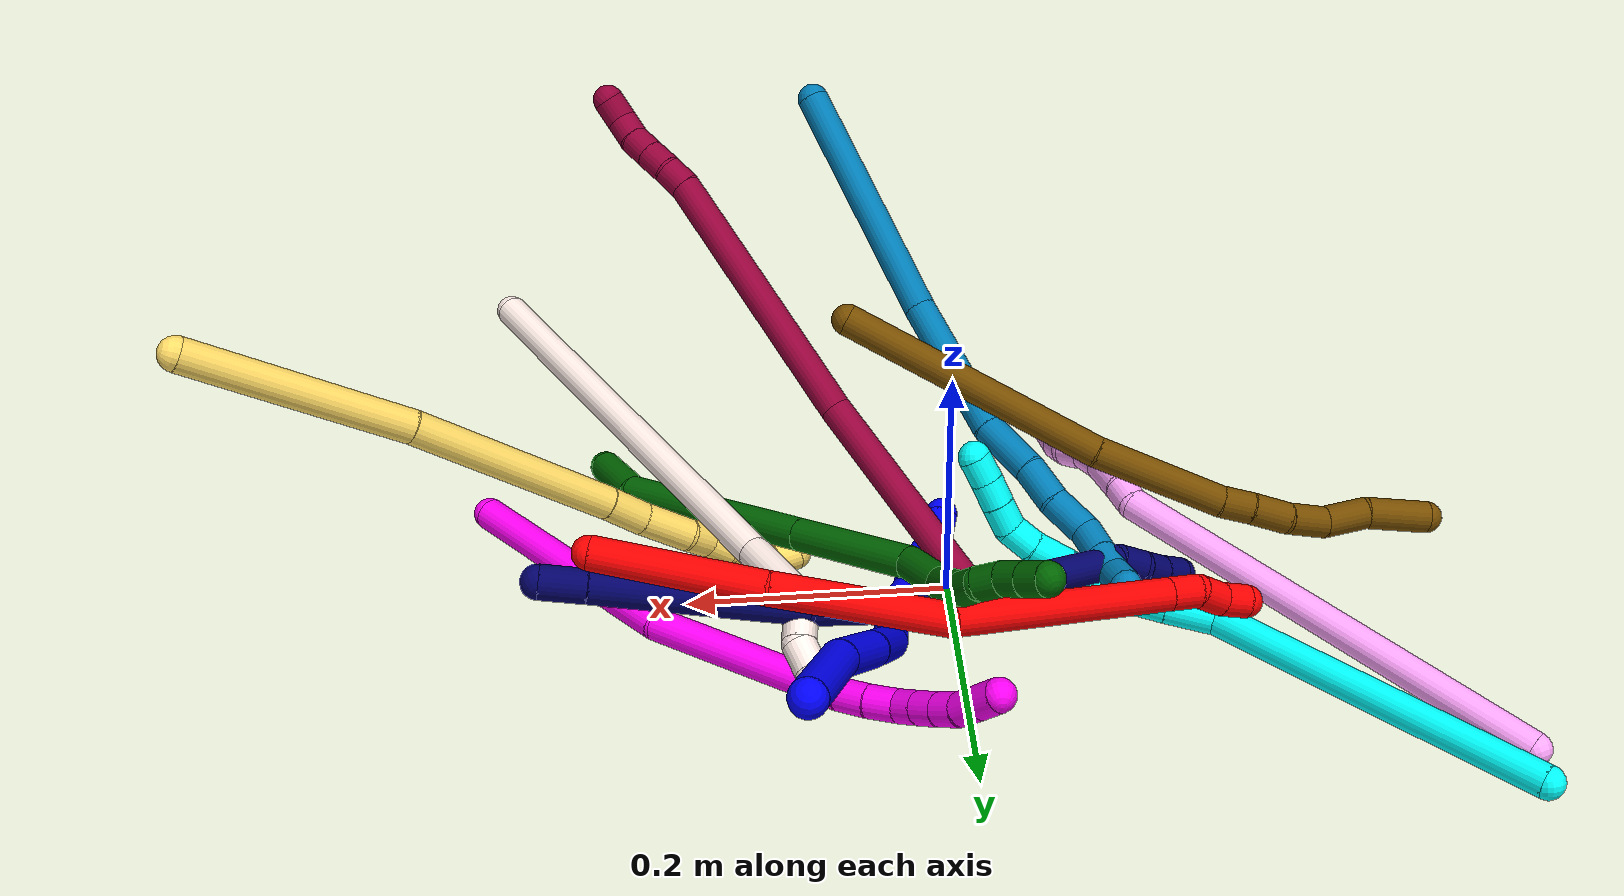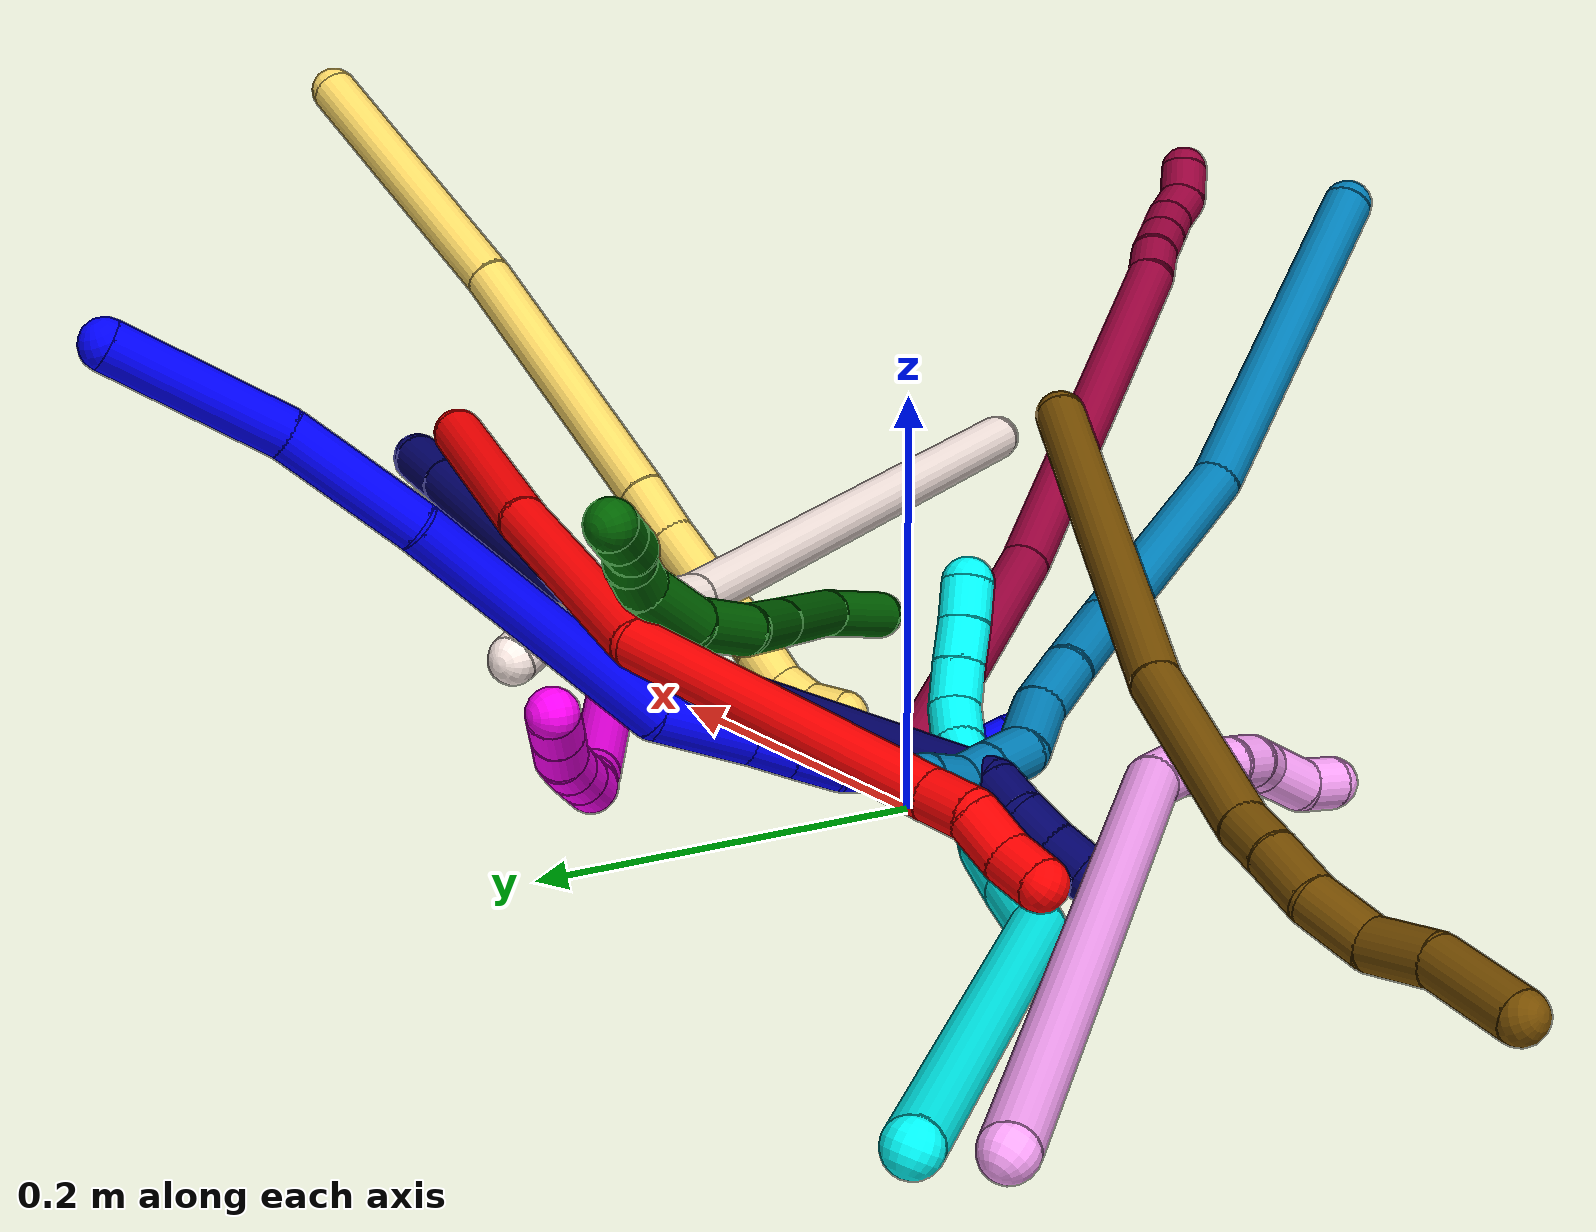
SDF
<sdf version="1.7">
 <world name="default">
  <plugin name="TubeGeneratorPlugin" filename="libtube_generator_plugin.so"/>
  <model name="photoneo_s_sensor">
   <static>1</static>
   <pose>0 0 2 1.57079 1.57079 3.14159</pose>
   <link name="link">
    <inertial><mass>0.1</mass></inertial>
    <sensor name="sensor" type="depth">
     <update_rate>30</update_rate>
     <camera>
      <horizontal_fov>1.22</horizontal_fov>
      <image><width>1920</width><height>1200</height><format>B8G8R8</format></image>
      <clip><near>0.1</near><far>4</far></clip>
      <depth_camera><output>points</output></depth_camera>
     </camera>
     <plugin name="camera_plugin" filename="libgazebo_ros_depth_camera.so">
      <baseline>0.2</baseline>
      <alwaysOn>1</alwaysOn>
      <updateRate>0.0</updateRate>
      <cameraName>camera_ir</cameraName>
      <imageTopicName>/camera/color/image_raw</imageTopicName>
      <cameraInfoTopicName>/camera/color/camera_info</cameraInfoTopicName>
      <depthImageTopicName>/camera/depth/image_raw</depthImageTopicName>
      <depthImageCameraInfoTopicName>/camera/depth/camera_info</depthImageCameraInfoTopicName>
      <pointCloudTopicName>/camera/depth/points</pointCloudTopicName>
      <frameName>fr_optical</frameName>
      <pointCloudCutoff>0.1</pointCloudCutoff>
      <pointCloudCutoffMax>2.0</pointCloudCutoffMax>
      <distortionK1>0</distortionK1>
      <distortionK2>0</distortionK2>
      <distortionK3>0</distortionK3>
      <distortionT1>0</distortionT1>
      <distortionT2>0</distortionT2>
      <CxPrime>0</CxPrime>
      <Cx>0</Cx>
      <Cy>0</Cy>
      <focalLength>0</focalLength>
      <hackBaseline>0</hackBaseline>
     </plugin>
    </sensor>
   </link>
  </model>
  <gravity>0 0 -9.8</gravity>
  <magnetic_field>6e-06 2.3e-05 -4.2e-05</magnetic_field>
  <atmosphere type="adiabatic"/>
  <physics name="default_physics" default="0" type="ode">
   <max_step_size>0.003</max_step_size>
   <real_time_factor>1</real_time_factor>
   <real_time_update_rate>1000</real_time_update_rate>
   <max_contacts>10000</max_contacts>
   <ode>
    <solver>
     <type>quick</type>
     <iters>100</iters>
     <sor>1.3</sor>
     <use_dynamic_moi_rescaling>0</use_dynamic_moi_rescaling>
    </solver>
    <constraints>
     <contact_max_correcting_vel>0</contact_max_correcting_vel>
     <contact_surface_layer>0.001</contact_surface_layer>
     <cfm>0</cfm>
     <erp>0.2</erp>
    </constraints>
   </ode>
  </physics>
  <scene><ambient>0.4 0.4 0.4 1</ambient><background>0.7 0.7 0.7 1</background><shadows>0</shadows></scene>
  <audio><device>default</device></audio>
  <spherical_coordinates>
   <surface_model>EARTH_WGS84</surface_model>
   <latitude_deg>0</latitude_deg>
   <longitude_deg>0</longitude_deg>
   <elevation>0</elevation>
   <heading_deg>0</heading_deg>
  </spherical_coordinates>
  <model name="bin">
   <static>1</static>
   <link name="bottom">
    <collision name="collision-bottom">
     <pose>0 0 -0.01 0 -0 0</pose>
     <geometry><box><size>0.8 0.6 0.02</size></box></geometry>
     <surface>
      <friction><ode><mu>100</mu><mu2>100</mu2></ode></friction>
      <contact><collide_bitmask>65535</collide_bitmask></contact>
     </surface>
    </collision>
   </link>
   <link name="west_wall">
    <collision name="collision-west_wall">
     <pose>-0.41 0 0.1 0 -0 0</pose>
     <geometry><box><size>0.02 0.6 0.2</size></box></geometry>
     <surface>
      <friction><ode><mu>100</mu><mu2>100</mu2></ode></friction>
      <contact><collide_bitmask>65535</collide_bitmask></contact>
     </surface>
    </collision>
   </link>
   <link name="east_wall">
    <collision name="collision-east_wall">
     <pose>0.41 0 0.1 0 -0 0</pose>
     <geometry><box><size>0.02 0.6 0.2</size></box></geometry>
     <surface>
      <friction><ode><mu>100</mu><mu2>100</mu2></ode></friction>
      <contact><collide_bitmask>65535</collide_bitmask></contact>
     </surface>
    </collision>
   </link>
   <link name="south_wall">
    <collision name="collision-south_wall">
     <pose>0 -0.31 0.1 0 -0 0</pose>
     <geometry><box><size>0.8 0.02 0.2</size></box></geometry>
     <surface>
      <friction><ode><mu>100</mu><mu2>100</mu2></ode></friction>
      <contact><collide_bitmask>65535</collide_bitmask></contact>
     </surface>
    </collision>
   </link>
   <link name="north_wall">
    <collision name="collision-north_wall">
     <pose>0 0.31 0.1 0 -0 0</pose>
     <geometry><box><size>0.8 0.02 0.2</size></box></geometry>
     <surface>
      <friction><ode><mu>100</mu><mu2>100</mu2></ode></friction>
      <contact><collide_bitmask>65535</collide_bitmask></contact>
     </surface>
    </collision>
   </link>
  </model>
  <model name="1">
   <static>0</static>
   <link name="1">
    <collision name="collision-cylinder-e_1_1_4">
     <pose>-0.006289 -0.028016 -0.034944 2.4658 -0.139505 -0.392552</pose>
     <geometry><cylinder><radius>0.0125</radius><length>0.090455</length></cylinder></geometry>
     <surface>
      <friction><ode><mu>1.16</mu><mu2>1.16</mu2><slip1>0</slip1><slip2>0</slip2></ode></friction>
      <contact><ode><kp>1e+06</kp><kd>1</kd><max_vel>0</max_vel><min_depth>0.001</min_depth></ode></contact>
     </surface>
    </collision>
    <visual name="visual-cylinder-e_1_1_4">
     <pose>-0.006289 -0.028016 -0.034944 2.4658 -0.139505 -0.392552</pose>
     <geometry><cylinder><radius>0.0125</radius><length>0.090455</length></cylinder></geometry>
     <material><ambient>0 0 1 1</ambient></material>
    </visual>
    <collision name="collision-cylinder-e_2_4_5">
     <pose>-0.021603 -0.073936 -0.100504 2.61243 -0.24916 -0.865923</pose>
     <geometry><cylinder><radius>0.0125</radius><length>0.073195</length></cylinder></geometry>
     <surface>
      <friction><ode><mu>1.16</mu><mu2>1.16</mu2><slip1>0</slip1><slip2>0</slip2></ode></friction>
      <contact><ode><kp>1e+06</kp><kd>1</kd><max_vel>0</max_vel><min_depth>0.001</min_depth></ode></contact>
     </surface>
    </collision>
    <visual name="visual-cylinder-e_2_4_5">
     <pose>-0.021603 -0.073936 -0.100504 2.61243 -0.24916 -0.865923</pose>
     <geometry><cylinder><radius>0.0125</radius><length>0.073195</length></cylinder></geometry>
     <material><ambient>0 0 1 1</ambient></material>
    </visual>
    <collision name="collision-cylinder-e_3_5_6">
     <pose>-0.037092 -0.124822 -0.198269 2.68502 -0.086198 -0.367061</pose>
     <geometry><cylinder><radius>0.0125</radius><length>0.150179</length></cylinder></geometry>
     <surface>
      <friction><ode><mu>1.16</mu><mu2>1.16</mu2><slip1>0</slip1><slip2>0</slip2></ode></friction>
      <contact><ode><kp>1e+06</kp><kd>1</kd><max_vel>0</max_vel><min_depth>0.001</min_depth></ode></contact>
     </surface>
    </collision>
    <visual name="visual-cylinder-e_3_5_6">
     <pose>-0.037092 -0.124822 -0.198269 2.68502 -0.086198 -0.367061</pose>
     <geometry><cylinder><radius>0.0125</radius><length>0.150179</length></cylinder></geometry>
     <material><ambient>0 0 1 1</ambient></material>
    </visual>
    <collision name="collision-cylinder-e_4_6_7">
     <pose>-0.042776 -0.177089 -0.283259 2.31734 0.029698 0.067914</pose>
     <geometry><cylinder><radius>0.0125</radius><length>0.052568</length></cylinder></geometry>
     <surface>
      <friction><ode><mu>1.16</mu><mu2>1.16</mu2><slip1>0</slip1><slip2>0</slip2></ode></friction>
      <contact><ode><kp>1e+06</kp><kd>1</kd><max_vel>0</max_vel><min_depth>0.001</min_depth></ode></contact>
     </surface>
    </collision>
    <visual name="visual-cylinder-e_4_6_7">
     <pose>-0.042776 -0.177089 -0.283259 2.31734 0.029698 0.067914</pose>
     <geometry><cylinder><radius>0.0125</radius><length>0.052568</length></cylinder></geometry>
     <material><ambient>0 0 1 1</ambient></material>
    </visual>
    <collision name="collision-cylinder-e_5_7_8">
     <pose>-0.044079 -0.205122 -0.308947 2.30193 -0.175489 -0.389171</pose>
     <geometry><cylinder><radius>0.0125</radius><length>0.02387</length></cylinder></geometry>
     <surface>
      <friction><ode><mu>1.16</mu><mu2>1.16</mu2><slip1>0</slip1><slip2>0</slip2></ode></friction>
      <contact><ode><kp>1e+06</kp><kd>1</kd><max_vel>0</max_vel><min_depth>0.001</min_depth></ode></contact>
     </surface>
    </collision>
    <visual name="visual-cylinder-e_5_7_8">
     <pose>-0.044079 -0.205122 -0.308947 2.30193 -0.175489 -0.389171</pose>
     <geometry><cylinder><radius>0.0125</radius><length>0.02387</length></cylinder></geometry>
     <material><ambient>0 0 1 1</ambient></material>
    </visual>
    <collision name="collision-cylinder-e_6_8_9">
     <pose>-0.048583 -0.222897 -0.324598 2.28363 -0.200114 -0.432126</pose>
     <geometry><cylinder><radius>0.0125</radius><length>0.024351</length></cylinder></geometry>
     <surface>
      <friction><ode><mu>1.16</mu><mu2>1.16</mu2><slip1>0</slip1><slip2>0</slip2></ode></friction>
      <contact><ode><kp>1e+06</kp><kd>1</kd><max_vel>0</max_vel><min_depth>0.001</min_depth></ode></contact>
     </surface>
    </collision>
    <visual name="visual-cylinder-e_6_8_9">
     <pose>-0.048583 -0.222897 -0.324598 2.28363 -0.200114 -0.432126</pose>
     <geometry><cylinder><radius>0.0125</radius><length>0.024351</length></cylinder></geometry>
     <material><ambient>0 0 1 1</ambient></material>
    </visual>
    <collision name="collision-cylinder-e_7_9_10">
     <pose>-0.054139 -0.249689 -0.340828 2.01372 -0.158133 -0.249257</pose>
     <geometry><cylinder><radius>0.0125</radius><length>0.03982</length></cylinder></geometry>
     <surface>
      <friction><ode><mu>1.16</mu><mu2>1.16</mu2><slip1>0</slip1><slip2>0</slip2></ode></friction>
      <contact><ode><kp>1e+06</kp><kd>1</kd><max_vel>0</max_vel><min_depth>0.001</min_depth></ode></contact>
     </surface>
    </collision>
    <visual name="visual-cylinder-e_7_9_10">
     <pose>-0.054139 -0.249689 -0.340828 2.01372 -0.158133 -0.249257</pose>
     <geometry><cylinder><radius>0.0125</radius><length>0.03982</length></cylinder></geometry>
     <material><ambient>0 0 1 1</ambient></material>
    </visual>
    <collision name="collision-cylinder-e_8_10_11">
     <pose>-0.062281 -0.277974 -0.350553 1.69361 -0.441259 -0.496853</pose>
     <geometry><cylinder><radius>0.0125</radius><length>0.023447</length></cylinder></geometry>
     <surface>
      <friction><ode><mu>1.16</mu><mu2>1.16</mu2><slip1>0</slip1><slip2>0</slip2></ode></friction>
      <contact><ode><kp>1e+06</kp><kd>1</kd><max_vel>0</max_vel><min_depth>0.001</min_depth></ode></contact>
     </surface>
    </collision>
    <visual name="visual-cylinder-e_8_10_11">
     <pose>-0.062281 -0.277974 -0.350553 1.69361 -0.441259 -0.496853</pose>
     <geometry><cylinder><radius>0.0125</radius><length>0.023447</length></cylinder></geometry>
     <material><ambient>0 0 1 1</ambient></material>
    </visual>
    <collision name="collision-cylinder-e_9_11_2">
     <pose>-0.067943 -0.299526 -0.351477 1.5368 -0.059298 -0.057317</pose>
     <geometry><cylinder><radius>0.0125</radius><length>0.022115</length></cylinder></geometry>
     <surface>
      <friction><ode><mu>1.16</mu><mu2>1.16</mu2><slip1>0</slip1><slip2>0</slip2></ode></friction>
      <contact><ode><kp>1e+06</kp><kd>1</kd><max_vel>0</max_vel><min_depth>0.001</min_depth></ode></contact>
     </surface>
    </collision>
    <visual name="visual-cylinder-e_9_11_2">
     <pose>-0.067943 -0.299526 -0.351477 1.5368 -0.059298 -0.057317</pose>
     <geometry><cylinder><radius>0.0125</radius><length>0.022115</length></cylinder></geometry>
     <material><ambient>0 0 1 1</ambient></material>
    </visual>
    <collision name="collision-sphere-2">
     <pose>-0.068598 -0.310558 -0.351101 0 -0 0</pose>
     <geometry><sphere><radius>0.0125</radius></sphere></geometry>
     <surface>
      <friction><ode><mu>1.16</mu><mu2>1.16</mu2><slip1>0</slip1><slip2>0</slip2></ode></friction>
      <contact><ode><kp>1e+06</kp><kd>1</kd><max_vel>0</max_vel><min_depth>0.001</min_depth></ode></contact>
     </surface>
    </collision>
    <visual name="visual-sphere-2">
     <pose>-0.068598 -0.310558 -0.351101 0 -0 0</pose>
     <geometry><sphere><radius>0.0125</radius></sphere></geometry>
     <material><ambient>0 0 1 1</ambient></material>
    </visual>
    <collision name="collision-sphere-11">
     <pose>-0.067288 -0.288495 -0.351852 0 -0 0</pose>
     <geometry><sphere><radius>0.0125</radius></sphere></geometry>
     <surface>
      <friction><ode><mu>1.16</mu><mu2>1.16</mu2><slip1>0</slip1><slip2>0</slip2></ode></friction>
      <contact><ode><kp>1e+06</kp><kd>1</kd><max_vel>0</max_vel><min_depth>0.001</min_depth></ode></contact>
     </surface>
    </collision>
    <visual name="visual-sphere-11">
     <pose>-0.067288 -0.288495 -0.351852 0 -0 0</pose>
     <geometry><sphere><radius>0.0125</radius></sphere></geometry>
     <material><ambient>0 0 1 1</ambient></material>
    </visual>
    <collision name="collision-sphere-10">
     <pose>-0.057274 -0.267453 -0.349254 0 -0 0</pose>
     <geometry><sphere><radius>0.0125</radius></sphere></geometry>
     <surface>
      <friction><ode><mu>1.16</mu><mu2>1.16</mu2><slip1>0</slip1><slip2>0</slip2></ode></friction>
      <contact><ode><kp>1e+06</kp><kd>1</kd><max_vel>0</max_vel><min_depth>0.001</min_depth></ode></contact>
     </surface>
    </collision>
    <visual name="visual-sphere-10">
     <pose>-0.057274 -0.267453 -0.349254 0 -0 0</pose>
     <geometry><sphere><radius>0.0125</radius></sphere></geometry>
     <material><ambient>0 0 1 1</ambient></material>
    </visual>
    <collision name="collision-sphere-9">
     <pose>-0.051003 -0.231924 -0.332401 0 -0 0</pose>
     <geometry><sphere><radius>0.0125</radius></sphere></geometry>
     <surface>
      <friction><ode><mu>1.16</mu><mu2>1.16</mu2><slip1>0</slip1><slip2>0</slip2></ode></friction>
      <contact><ode><kp>1e+06</kp><kd>1</kd><max_vel>0</max_vel><min_depth>0.001</min_depth></ode></contact>
     </surface>
    </collision>
    <visual name="visual-sphere-9">
     <pose>-0.051003 -0.231924 -0.332401 0 -0 0</pose>
     <geometry><sphere><radius>0.0125</radius></sphere></geometry>
     <material><ambient>0 0 1 1</ambient></material>
    </visual>
    <collision name="collision-sphere-4">
     <pose>-0.012578 -0.056031 -0.069888 0 -0 0</pose>
     <geometry><sphere><radius>0.0125</radius></sphere></geometry>
     <surface>
      <friction><ode><mu>1.16</mu><mu2>1.16</mu2><slip1>0</slip1><slip2>0</slip2></ode></friction>
      <contact><ode><kp>1e+06</kp><kd>1</kd><max_vel>0</max_vel><min_depth>0.001</min_depth></ode></contact>
     </surface>
    </collision>
    <visual name="visual-sphere-4">
     <pose>-0.012578 -0.056031 -0.069888 0 -0 0</pose>
     <geometry><sphere><radius>0.0125</radius></sphere></geometry>
     <material><ambient>0 0 1 1</ambient></material>
    </visual>
    <collision name="collision-sphere-1">
     <geometry><sphere><radius>0.0125</radius></sphere></geometry>
     <surface>
      <friction><ode><mu>1.16</mu><mu2>1.16</mu2><slip1>0</slip1><slip2>0</slip2></ode></friction>
      <contact><ode><kp>1e+06</kp><kd>1</kd><max_vel>0</max_vel><min_depth>0.001</min_depth></ode></contact>
     </surface>
    </collision>
    <visual name="visual-sphere-1">
     <geometry><sphere><radius>0.0125</radius></sphere></geometry>
     <material><ambient>0 0 1 1</ambient></material>
    </visual>
    <collision name="collision-sphere-8">
     <pose>-0.046163 -0.21387 -0.316794 0 -0 0</pose>
     <geometry><sphere><radius>0.0125</radius></sphere></geometry>
     <surface>
      <friction><ode><mu>1.16</mu><mu2>1.16</mu2><slip1>0</slip1><slip2>0</slip2></ode></friction>
      <contact><ode><kp>1e+06</kp><kd>1</kd><max_vel>0</max_vel><min_depth>0.001</min_depth></ode></contact>
     </surface>
    </collision>
    <visual name="visual-sphere-8">
     <pose>-0.046163 -0.21387 -0.316794 0 -0 0</pose>
     <geometry><sphere><radius>0.0125</radius></sphere></geometry>
     <material><ambient>0 0 1 1</ambient></material>
    </visual>
    <collision name="collision-sphere-5">
     <pose>-0.030627 -0.09184 -0.131121 0 -0 0</pose>
     <geometry><sphere><radius>0.0125</radius></sphere></geometry>
     <surface>
      <friction><ode><mu>1.16</mu><mu2>1.16</mu2><slip1>0</slip1><slip2>0</slip2></ode></friction>
      <contact><ode><kp>1e+06</kp><kd>1</kd><max_vel>0</max_vel><min_depth>0.001</min_depth></ode></contact>
     </surface>
    </collision>
    <visual name="visual-sphere-5">
     <pose>-0.030627 -0.09184 -0.131121 0 -0 0</pose>
     <geometry><sphere><radius>0.0125</radius></sphere></geometry>
     <material><ambient>0 0 1 1</ambient></material>
    </visual>
    <collision name="collision-sphere-6">
     <pose>-0.043556 -0.157804 -0.265417 0 -0 0</pose>
     <geometry><sphere><radius>0.0125</radius></sphere></geometry>
     <surface>
      <friction><ode><mu>1.16</mu><mu2>1.16</mu2><slip1>0</slip1><slip2>0</slip2></ode></friction>
      <contact><ode><kp>1e+06</kp><kd>1</kd><max_vel>0</max_vel><min_depth>0.001</min_depth></ode></contact>
     </surface>
    </collision>
    <visual name="visual-sphere-6">
     <pose>-0.043556 -0.157804 -0.265417 0 -0 0</pose>
     <geometry><sphere><radius>0.0125</radius></sphere></geometry>
     <material><ambient>0 0 1 1</ambient></material>
    </visual>
    <collision name="collision-sphere-7">
     <pose>-0.041995 -0.196374 -0.301101 0 -0 0</pose>
     <geometry><sphere><radius>0.0125</radius></sphere></geometry>
     <surface>
      <friction><ode><mu>1.16</mu><mu2>1.16</mu2><slip1>0</slip1><slip2>0</slip2></ode></friction>
      <contact><ode><kp>1e+06</kp><kd>1</kd><max_vel>0</max_vel><min_depth>0.001</min_depth></ode></contact>
     </surface>
    </collision>
    <visual name="visual-sphere-7">
     <pose>-0.041995 -0.196374 -0.301101 0 -0 0</pose>
     <geometry><sphere><radius>0.0125</radius></sphere></geometry>
     <material><ambient>0 0 1 1</ambient></material>
    </visual>
    <inertial>
     <pose>-0.034646 -0.138818 -0.200053 0 -0 0</pose>
     <mass>0.5</mass>
     <inertia>
      <ixx>0.000215</ixx>
      <ixy>0</ixy>
      <ixz>0</ixz>
      <iyy>-0.000495</iyy>
      <iyz>0</iyz>
      <izz>0.000225</izz>
     </inertia>
    </inertial>
   </link>
   <pose>0.124016 0.343744 0.240234 -0.385394 -0.113794 -0.197492</pose>
  </model>
  <model name="2">
   <static>0</static>
   <link name="2">
    <collision name="collision-cylinder-e_1_1_4">
     <pose>0.007875 -0.061013 0.004678 1.49427 0.12799 0.118575</pose>
     <geometry><cylinder><radius>0.0125</radius><length>0.123394</length></cylinder></geometry>
     <surface>
      <friction><ode><mu>1.16</mu><mu2>1.16</mu2><slip1>0</slip1><slip2>0</slip2></ode></friction>
      <contact><ode><kp>1e+06</kp><kd>1</kd><max_vel>0</max_vel><min_depth>0.001</min_depth></ode></contact>
     </surface>
    </collision>
    <visual name="visual-cylinder-e_1_1_4">
     <pose>0.007875 -0.061013 0.004678 1.49427 0.12799 0.118575</pose>
     <geometry><cylinder><radius>0.0125</radius><length>0.123394</length></cylinder></geometry>
     <material><ambient>1 0 0 1</ambient></material>
    </visual>
    <collision name="collision-cylinder-e_2_4_5">
     <pose>0.023923 -0.186225 0.003713 1.65848 0.126145 0.137685</pose>
     <geometry><cylinder><radius>0.0125</radius><length>0.129924</length></cylinder></geometry>
     <surface>
      <friction><ode><mu>1.16</mu><mu2>1.16</mu2><slip1>0</slip1><slip2>0</slip2></ode></friction>
      <contact><ode><kp>1e+06</kp><kd>1</kd><max_vel>0</max_vel><min_depth>0.001</min_depth></ode></contact>
     </surface>
    </collision>
    <visual name="visual-cylinder-e_2_4_5">
     <pose>0.023923 -0.186225 0.003713 1.65848 0.126145 0.137685</pose>
     <geometry><cylinder><radius>0.0125</radius><length>0.129924</length></cylinder></geometry>
     <material><ambient>1 0 0 1</ambient></material>
    </visual>
    <collision name="collision-cylinder-e_3_5_6">
     <pose>0.059881 -0.326784 -0.036317 1.99391 0.32035 0.489838</pose>
     <geometry><cylinder><radius>0.0125</radius><length>0.17647</length></cylinder></geometry>
     <surface>
      <friction><ode><mu>1.16</mu><mu2>1.16</mu2><slip1>0</slip1><slip2>0</slip2></ode></friction>
      <contact><ode><kp>1e+06</kp><kd>1</kd><max_vel>0</max_vel><min_depth>0.001</min_depth></ode></contact>
     </surface>
    </collision>
    <visual name="visual-cylinder-e_3_5_6">
     <pose>0.059881 -0.326784 -0.036317 1.99391 0.32035 0.489838</pose>
     <geometry><cylinder><radius>0.0125</radius><length>0.17647</length></cylinder></geometry>
     <material><ambient>1 0 0 1</ambient></material>
    </visual>
    <collision name="collision-cylinder-e_4_6_7">
     <pose>0.091829 -0.413974 -0.074291 1.89078 0.349874 0.480084</pose>
     <geometry><cylinder><radius>0.0125</radius><length>0.024288</length></cylinder></geometry>
     <surface>
      <friction><ode><mu>1.16</mu><mu2>1.16</mu2><slip1>0</slip1><slip2>0</slip2></ode></friction>
      <contact><ode><kp>1e+06</kp><kd>1</kd><max_vel>0</max_vel><min_depth>0.001</min_depth></ode></contact>
     </surface>
    </collision>
    <visual name="visual-cylinder-e_4_6_7">
     <pose>0.091829 -0.413974 -0.074291 1.89078 0.349874 0.480084</pose>
     <geometry><cylinder><radius>0.0125</radius><length>0.024288</length></cylinder></geometry>
     <material><ambient>1 0 0 1</ambient></material>
    </visual>
    <collision name="collision-cylinder-e_5_7_8">
     <pose>0.095021 -0.435229 -0.084118 2.11004 -0.079707 -0.140429</pose>
     <geometry><cylinder><radius>0.0125</radius><length>0.024376</length></cylinder></geometry>
     <surface>
      <friction><ode><mu>1.16</mu><mu2>1.16</mu2><slip1>0</slip1><slip2>0</slip2></ode></friction>
      <contact><ode><kp>1e+06</kp><kd>1</kd><max_vel>0</max_vel><min_depth>0.001</min_depth></ode></contact>
     </surface>
    </collision>
    <visual name="visual-cylinder-e_5_7_8">
     <pose>0.095021 -0.435229 -0.084118 2.11004 -0.079707 -0.140429</pose>
     <geometry><cylinder><radius>0.0125</radius><length>0.024376</length></cylinder></geometry>
     <material><ambient>1 0 0 1</ambient></material>
    </visual>
    <collision name="collision-cylinder-e_6_8_2">
     <pose>0.095841 -0.455748 -0.093671 1.88801 0.166946 0.230038</pose>
     <geometry><cylinder><radius>0.0125</radius><length>0.021548</length></cylinder></geometry>
     <surface>
      <friction><ode><mu>1.16</mu><mu2>1.16</mu2><slip1>0</slip1><slip2>0</slip2></ode></friction>
      <contact><ode><kp>1e+06</kp><kd>1</kd><max_vel>0</max_vel><min_depth>0.001</min_depth></ode></contact>
     </surface>
    </collision>
    <visual name="visual-cylinder-e_6_8_2">
     <pose>0.095841 -0.455748 -0.093671 1.88801 0.166946 0.230038</pose>
     <geometry><cylinder><radius>0.0125</radius><length>0.021548</length></cylinder></geometry>
     <material><ambient>1 0 0 1</ambient></material>
    </visual>
    <collision name="collision-sphere-2">
     <pose>0.097631 -0.465842 -0.096984 0 -0 0</pose>
     <geometry><sphere><radius>0.0125</radius></sphere></geometry>
     <surface>
      <friction><ode><mu>1.16</mu><mu2>1.16</mu2><slip1>0</slip1><slip2>0</slip2></ode></friction>
      <contact><ode><kp>1e+06</kp><kd>1</kd><max_vel>0</max_vel><min_depth>0.001</min_depth></ode></contact>
     </surface>
    </collision>
    <visual name="visual-sphere-2">
     <pose>0.097631 -0.465842 -0.096984 0 -0 0</pose>
     <geometry><sphere><radius>0.0125</radius></sphere></geometry>
     <material><ambient>1 0 0 1</ambient></material>
    </visual>
    <collision name="collision-sphere-4">
     <pose>0.01575 -0.122027 0.009357 0 -0 0</pose>
     <geometry><sphere><radius>0.0125</radius></sphere></geometry>
     <surface>
      <friction><ode><mu>1.16</mu><mu2>1.16</mu2><slip1>0</slip1><slip2>0</slip2></ode></friction>
      <contact><ode><kp>1e+06</kp><kd>1</kd><max_vel>0</max_vel><min_depth>0.001</min_depth></ode></contact>
     </surface>
    </collision>
    <visual name="visual-sphere-4">
     <pose>0.01575 -0.122027 0.009357 0 -0 0</pose>
     <geometry><sphere><radius>0.0125</radius></sphere></geometry>
     <material><ambient>1 0 0 1</ambient></material>
    </visual>
    <collision name="collision-sphere-1">
     <geometry><sphere><radius>0.0125</radius></sphere></geometry>
     <surface>
      <friction><ode><mu>1.16</mu><mu2>1.16</mu2><slip1>0</slip1><slip2>0</slip2></ode></friction>
      <contact><ode><kp>1e+06</kp><kd>1</kd><max_vel>0</max_vel><min_depth>0.001</min_depth></ode></contact>
     </surface>
    </collision>
    <visual name="visual-sphere-1">
     <geometry><sphere><radius>0.0125</radius></sphere></geometry>
     <material><ambient>1 0 0 1</ambient></material>
    </visual>
    <collision name="collision-sphere-8">
     <pose>0.094051 -0.445654 -0.090357 0 -0 0</pose>
     <geometry><sphere><radius>0.0125</radius></sphere></geometry>
     <surface>
      <friction><ode><mu>1.16</mu><mu2>1.16</mu2><slip1>0</slip1><slip2>0</slip2></ode></friction>
      <contact><ode><kp>1e+06</kp><kd>1</kd><max_vel>0</max_vel><min_depth>0.001</min_depth></ode></contact>
     </surface>
    </collision>
    <visual name="visual-sphere-8">
     <pose>0.094051 -0.445654 -0.090357 0 -0 0</pose>
     <geometry><sphere><radius>0.0125</radius></sphere></geometry>
     <material><ambient>1 0 0 1</ambient></material>
    </visual>
    <collision name="collision-sphere-5">
     <pose>0.032096 -0.250424 -0.00193 0 -0 0</pose>
     <geometry><sphere><radius>0.0125</radius></sphere></geometry>
     <surface>
      <friction><ode><mu>1.16</mu><mu2>1.16</mu2><slip1>0</slip1><slip2>0</slip2></ode></friction>
      <contact><ode><kp>1e+06</kp><kd>1</kd><max_vel>0</max_vel><min_depth>0.001</min_depth></ode></contact>
     </surface>
    </collision>
    <visual name="visual-sphere-5">
     <pose>0.032096 -0.250424 -0.00193 0 -0 0</pose>
     <geometry><sphere><radius>0.0125</radius></sphere></geometry>
     <material><ambient>1 0 0 1</ambient></material>
    </visual>
    <collision name="collision-sphere-6">
     <pose>0.087666 -0.403145 -0.070703 0 -0 0</pose>
     <geometry><sphere><radius>0.0125</radius></sphere></geometry>
     <surface>
      <friction><ode><mu>1.16</mu><mu2>1.16</mu2><slip1>0</slip1><slip2>0</slip2></ode></friction>
      <contact><ode><kp>1e+06</kp><kd>1</kd><max_vel>0</max_vel><min_depth>0.001</min_depth></ode></contact>
     </surface>
    </collision>
    <visual name="visual-sphere-6">
     <pose>0.087666 -0.403145 -0.070703 0 -0 0</pose>
     <geometry><sphere><radius>0.0125</radius></sphere></geometry>
     <material><ambient>1 0 0 1</ambient></material>
    </visual>
    <collision name="collision-sphere-7">
     <pose>0.095991 -0.424803 -0.07788 0 -0 0</pose>
     <geometry><sphere><radius>0.0125</radius></sphere></geometry>
     <surface>
      <friction><ode><mu>1.16</mu><mu2>1.16</mu2><slip1>0</slip1><slip2>0</slip2></ode></friction>
      <contact><ode><kp>1e+06</kp><kd>1</kd><max_vel>0</max_vel><min_depth>0.001</min_depth></ode></contact>
     </surface>
    </collision>
    <visual name="visual-sphere-7">
     <pose>0.095991 -0.424803 -0.07788 0 -0 0</pose>
     <geometry><sphere><radius>0.0125</radius></sphere></geometry>
     <material><ambient>1 0 0 1</ambient></material>
    </visual>
    <inertial>
     <pose>0.042518 -0.239751 -0.022445 0 -0 0</pose>
     <mass>0.5</mass>
     <inertia>
      <ixx>0.000999</ixx>
      <ixy>0</ixy>
      <ixz>0</ixz>
      <iyy>0.000111</iyy>
      <iyz>0</iyz>
      <izz>0.000554</izz>
     </inertia>
    </inertial>
   </link>
   <pose>0.260045 0.100577 0.146014 0.488238 -0.915397 -2.20452</pose>
  </model>
  <model name="3">
   <static>0</static>
   <link name="3">
    <collision name="collision-cylinder-e_1_1_4">
     <pose>0.104567 -0.066204 -0.048378 2.20186 0.905792 1.52823</pose>
     <geometry><cylinder><radius>0.0125</radius><length>0.265764</length></cylinder></geometry>
     <surface>
      <friction><ode><mu>1.16</mu><mu2>1.16</mu2><slip1>0</slip1><slip2>0</slip2></ode></friction>
      <contact><ode><kp>1e+06</kp><kd>1</kd><max_vel>0</max_vel><min_depth>0.001</min_depth></ode></contact>
     </surface>
    </collision>
    <visual name="visual-cylinder-e_1_1_4">
     <pose>0.104567 -0.066204 -0.048378 2.20186 0.905792 1.52823</pose>
     <geometry><cylinder><radius>0.0125</radius><length>0.265764</length></cylinder></geometry>
     <material><ambient>0.003922 1 0.996078 1</ambient></material>
    </visual>
    <collision name="collision-cylinder-e_2_4_5">
     <pose>0.21804 -0.148694 -0.102629 1.91687 0.475158 0.663943</pose>
     <geometry><cylinder><radius>0.0125</radius><length>0.038938</length></cylinder></geometry>
     <surface>
      <friction><ode><mu>1.16</mu><mu2>1.16</mu2><slip1>0</slip1><slip2>0</slip2></ode></friction>
      <contact><ode><kp>1e+06</kp><kd>1</kd><max_vel>0</max_vel><min_depth>0.001</min_depth></ode></contact>
     </surface>
    </collision>
    <visual name="visual-cylinder-e_2_4_5">
     <pose>0.21804 -0.148694 -0.102629 1.91687 0.475158 0.663943</pose>
     <geometry><cylinder><radius>0.0125</radius><length>0.038938</length></cylinder></geometry>
     <material><ambient>0.003922 1 0.996078 1</ambient></material>
    </visual>
    <collision name="collision-cylinder-e_3_5_6">
     <pose>0.236718 -0.182719 -0.115673 1.95501 0.472171 0.68536</pose>
     <geometry><cylinder><radius>0.0125</radius><length>0.04297</length></cylinder></geometry>
     <surface>
      <friction><ode><mu>1.16</mu><mu2>1.16</mu2><slip1>0</slip1><slip2>0</slip2></ode></friction>
      <contact><ode><kp>1e+06</kp><kd>1</kd><max_vel>0</max_vel><min_depth>0.001</min_depth></ode></contact>
     </surface>
    </collision>
    <visual name="visual-cylinder-e_3_5_6">
     <pose>0.236718 -0.182719 -0.115673 1.95501 0.472171 0.68536</pose>
     <geometry><cylinder><radius>0.0125</radius><length>0.04297</length></cylinder></geometry>
     <material><ambient>0.003922 1 0.996078 1</ambient></material>
    </visual>
    <collision name="collision-cylinder-e_4_6_7">
     <pose>0.252327 -0.214367 -0.13483 2.28201 0.307791 0.652651</pose>
     <geometry><cylinder><radius>0.0125</radius><length>0.038532</length></cylinder></geometry>
     <surface>
      <friction><ode><mu>1.16</mu><mu2>1.16</mu2><slip1>0</slip1><slip2>0</slip2></ode></friction>
      <contact><ode><kp>1e+06</kp><kd>1</kd><max_vel>0</max_vel><min_depth>0.001</min_depth></ode></contact>
     </surface>
    </collision>
    <visual name="visual-cylinder-e_4_6_7">
     <pose>0.252327 -0.214367 -0.13483 2.28201 0.307791 0.652651</pose>
     <geometry><cylinder><radius>0.0125</radius><length>0.038532</length></cylinder></geometry>
     <material><ambient>0.003922 1 0.996078 1</ambient></material>
    </visual>
    <collision name="collision-cylinder-e_5_7_8">
     <pose>0.262062 -0.239676 -0.155153 2.20235 0.269301 0.521715</pose>
     <geometry><cylinder><radius>0.0125</radius><length>0.029303</length></cylinder></geometry>
     <surface>
      <friction><ode><mu>1.16</mu><mu2>1.16</mu2><slip1>0</slip1><slip2>0</slip2></ode></friction>
      <contact><ode><kp>1e+06</kp><kd>1</kd><max_vel>0</max_vel><min_depth>0.001</min_depth></ode></contact>
     </surface>
    </collision>
    <visual name="visual-cylinder-e_5_7_8">
     <pose>0.262062 -0.239676 -0.155153 2.20235 0.269301 0.521715</pose>
     <geometry><cylinder><radius>0.0125</radius><length>0.029303</length></cylinder></geometry>
     <material><ambient>0.003922 1 0.996078 1</ambient></material>
    </visual>
    <collision name="collision-cylinder-e_6_8_9">
     <pose>0.268983 -0.258554 -0.171486 2.38949 0.269456 0.661391</pose>
     <geometry><cylinder><radius>0.0125</radius><length>0.022715</length></cylinder></geometry>
     <surface>
      <friction><ode><mu>1.16</mu><mu2>1.16</mu2><slip1>0</slip1><slip2>0</slip2></ode></friction>
      <contact><ode><kp>1e+06</kp><kd>1</kd><max_vel>0</max_vel><min_depth>0.001</min_depth></ode></contact>
     </surface>
    </collision>
    <visual name="visual-cylinder-e_6_8_9">
     <pose>0.268983 -0.258554 -0.171486 2.38949 0.269456 0.661391</pose>
     <geometry><cylinder><radius>0.0125</radius><length>0.022715</length></cylinder></geometry>
     <material><ambient>0.003922 1 0.996078 1</ambient></material>
    </visual>
    <collision name="collision-cylinder-e_7_9_10">
     <pose>0.272116 -0.269798 -0.189516 2.78263 0.010213 0.056276</pose>
     <geometry><cylinder><radius>0.0125</radius><length>0.021438</length></cylinder></geometry>
     <surface>
      <friction><ode><mu>1.16</mu><mu2>1.16</mu2><slip1>0</slip1><slip2>0</slip2></ode></friction>
      <contact><ode><kp>1e+06</kp><kd>1</kd><max_vel>0</max_vel><min_depth>0.001</min_depth></ode></contact>
     </surface>
    </collision>
    <visual name="visual-cylinder-e_7_9_10">
     <pose>0.272116 -0.269798 -0.189516 2.78263 0.010213 0.056276</pose>
     <geometry><cylinder><radius>0.0125</radius><length>0.021438</length></cylinder></geometry>
     <material><ambient>0.003922 1 0.996078 1</ambient></material>
    </visual>
    <collision name="collision-cylinder-e_8_10_11">
     <pose>0.272663 -0.276886 -0.209085 2.80631 0.04332 0.254633</pose>
     <geometry><cylinder><radius>0.0125</radius><length>0.02021</length></cylinder></geometry>
     <surface>
      <friction><ode><mu>1.16</mu><mu2>1.16</mu2><slip1>0</slip1><slip2>0</slip2></ode></friction>
      <contact><ode><kp>1e+06</kp><kd>1</kd><max_vel>0</max_vel><min_depth>0.001</min_depth></ode></contact>
     </surface>
    </collision>
    <visual name="visual-cylinder-e_8_10_11">
     <pose>0.272663 -0.276886 -0.209085 2.80631 0.04332 0.254633</pose>
     <geometry><cylinder><radius>0.0125</radius><length>0.02021</length></cylinder></geometry>
     <material><ambient>0.003922 1 0.996078 1</ambient></material>
    </visual>
    <collision name="collision-cylinder-e_9_11_2">
     <pose>0.273292 -0.283927 -0.227969 2.76302 0.01905 0.099359</pose>
     <geometry><cylinder><radius>0.0125</radius><length>0.020131</length></cylinder></geometry>
     <surface>
      <friction><ode><mu>1.16</mu><mu2>1.16</mu2><slip1>0</slip1><slip2>0</slip2></ode></friction>
      <contact><ode><kp>1e+06</kp><kd>1</kd><max_vel>0</max_vel><min_depth>0.001</min_depth></ode></contact>
     </surface>
    </collision>
    <visual name="visual-cylinder-e_9_11_2">
     <pose>0.273292 -0.283927 -0.227969 2.76302 0.01905 0.099359</pose>
     <geometry><cylinder><radius>0.0125</radius><length>0.020131</length></cylinder></geometry>
     <material><ambient>0.003922 1 0.996078 1</ambient></material>
    </visual>
    <collision name="collision-sphere-2">
     <pose>0.273484 -0.287646 -0.23732 0 -0 0</pose>
     <geometry><sphere><radius>0.0125</radius></sphere></geometry>
     <surface>
      <friction><ode><mu>1.16</mu><mu2>1.16</mu2><slip1>0</slip1><slip2>0</slip2></ode></friction>
      <contact><ode><kp>1e+06</kp><kd>1</kd><max_vel>0</max_vel><min_depth>0.001</min_depth></ode></contact>
     </surface>
    </collision>
    <visual name="visual-sphere-2">
     <pose>0.273484 -0.287646 -0.23732 0 -0 0</pose>
     <geometry><sphere><radius>0.0125</radius></sphere></geometry>
     <material><ambient>0.003922 1 0.996078 1</ambient></material>
    </visual>
    <collision name="collision-sphere-11">
     <pose>0.273101 -0.280207 -0.218618 0 -0 0</pose>
     <geometry><sphere><radius>0.0125</radius></sphere></geometry>
     <surface>
      <friction><ode><mu>1.16</mu><mu2>1.16</mu2><slip1>0</slip1><slip2>0</slip2></ode></friction>
      <contact><ode><kp>1e+06</kp><kd>1</kd><max_vel>0</max_vel><min_depth>0.001</min_depth></ode></contact>
     </surface>
    </collision>
    <visual name="visual-sphere-11">
     <pose>0.273101 -0.280207 -0.218618 0 -0 0</pose>
     <geometry><sphere><radius>0.0125</radius></sphere></geometry>
     <material><ambient>0.003922 1 0.996078 1</ambient></material>
    </visual>
    <collision name="collision-sphere-10">
     <pose>0.272225 -0.273564 -0.199552 0 -0 0</pose>
     <geometry><sphere><radius>0.0125</radius></sphere></geometry>
     <surface>
      <friction><ode><mu>1.16</mu><mu2>1.16</mu2><slip1>0</slip1><slip2>0</slip2></ode></friction>
      <contact><ode><kp>1e+06</kp><kd>1</kd><max_vel>0</max_vel><min_depth>0.001</min_depth></ode></contact>
     </surface>
    </collision>
    <visual name="visual-sphere-10">
     <pose>0.272225 -0.273564 -0.199552 0 -0 0</pose>
     <geometry><sphere><radius>0.0125</radius></sphere></geometry>
     <material><ambient>0.003922 1 0.996078 1</ambient></material>
    </visual>
    <collision name="collision-sphere-9">
     <pose>0.272007 -0.266033 -0.179481 0 -0 0</pose>
     <geometry><sphere><radius>0.0125</radius></sphere></geometry>
     <surface>
      <friction><ode><mu>1.16</mu><mu2>1.16</mu2><slip1>0</slip1><slip2>0</slip2></ode></friction>
      <contact><ode><kp>1e+06</kp><kd>1</kd><max_vel>0</max_vel><min_depth>0.001</min_depth></ode></contact>
     </surface>
    </collision>
    <visual name="visual-sphere-9">
     <pose>0.272007 -0.266033 -0.179481 0 -0 0</pose>
     <geometry><sphere><radius>0.0125</radius></sphere></geometry>
     <material><ambient>0.003922 1 0.996078 1</ambient></material>
    </visual>
    <collision name="collision-sphere-4">
     <pose>0.209133 -0.132408 -0.096756 0 -0 0</pose>
     <geometry><sphere><radius>0.0125</radius></sphere></geometry>
     <surface>
      <friction><ode><mu>1.16</mu><mu2>1.16</mu2><slip1>0</slip1><slip2>0</slip2></ode></friction>
      <contact><ode><kp>1e+06</kp><kd>1</kd><max_vel>0</max_vel><min_depth>0.001</min_depth></ode></contact>
     </surface>
    </collision>
    <visual name="visual-sphere-4">
     <pose>0.209133 -0.132408 -0.096756 0 -0 0</pose>
     <geometry><sphere><radius>0.0125</radius></sphere></geometry>
     <material><ambient>0.003922 1 0.996078 1</ambient></material>
    </visual>
    <collision name="collision-sphere-1">
     <geometry><sphere><radius>0.0125</radius></sphere></geometry>
     <surface>
      <friction><ode><mu>1.16</mu><mu2>1.16</mu2><slip1>0</slip1><slip2>0</slip2></ode></friction>
      <contact><ode><kp>1e+06</kp><kd>1</kd><max_vel>0</max_vel><min_depth>0.001</min_depth></ode></contact>
     </surface>
    </collision>
    <visual name="visual-sphere-1">
     <geometry><sphere><radius>0.0125</radius></sphere></geometry>
     <material><ambient>0.003922 1 0.996078 1</ambient></material>
    </visual>
    <collision name="collision-sphere-8">
     <pose>0.26596 -0.251075 -0.163492 0 -0 0</pose>
     <geometry><sphere><radius>0.0125</radius></sphere></geometry>
     <surface>
      <friction><ode><mu>1.16</mu><mu2>1.16</mu2><slip1>0</slip1><slip2>0</slip2></ode></friction>
      <contact><ode><kp>1e+06</kp><kd>1</kd><max_vel>0</max_vel><min_depth>0.001</min_depth></ode></contact>
     </surface>
    </collision>
    <visual name="visual-sphere-8">
     <pose>0.26596 -0.251075 -0.163492 0 -0 0</pose>
     <geometry><sphere><radius>0.0125</radius></sphere></geometry>
     <material><ambient>0.003922 1 0.996078 1</ambient></material>
    </visual>
    <collision name="collision-sphere-5">
     <pose>0.226947 -0.16498 -0.108501 0 -0 0</pose>
     <geometry><sphere><radius>0.0125</radius></sphere></geometry>
     <surface>
      <friction><ode><mu>1.16</mu><mu2>1.16</mu2><slip1>0</slip1><slip2>0</slip2></ode></friction>
      <contact><ode><kp>1e+06</kp><kd>1</kd><max_vel>0</max_vel><min_depth>0.001</min_depth></ode></contact>
     </surface>
    </collision>
    <visual name="visual-sphere-5">
     <pose>0.226947 -0.16498 -0.108501 0 -0 0</pose>
     <geometry><sphere><radius>0.0125</radius></sphere></geometry>
     <material><ambient>0.003922 1 0.996078 1</ambient></material>
    </visual>
    <collision name="collision-sphere-6">
     <pose>0.24649 -0.200458 -0.122845 0 -0 0</pose>
     <geometry><sphere><radius>0.0125</radius></sphere></geometry>
     <surface>
      <friction><ode><mu>1.16</mu><mu2>1.16</mu2><slip1>0</slip1><slip2>0</slip2></ode></friction>
      <contact><ode><kp>1e+06</kp><kd>1</kd><max_vel>0</max_vel><min_depth>0.001</min_depth></ode></contact>
     </surface>
    </collision>
    <visual name="visual-sphere-6">
     <pose>0.24649 -0.200458 -0.122845 0 -0 0</pose>
     <geometry><sphere><radius>0.0125</radius></sphere></geometry>
     <material><ambient>0.003922 1 0.996078 1</ambient></material>
    </visual>
    <collision name="collision-sphere-7">
     <pose>0.258163 -0.228276 -0.146815 0 -0 0</pose>
     <geometry><sphere><radius>0.0125</radius></sphere></geometry>
     <surface>
      <friction><ode><mu>1.16</mu><mu2>1.16</mu2><slip1>0</slip1><slip2>0</slip2></ode></friction>
      <contact><ode><kp>1e+06</kp><kd>1</kd><max_vel>0</max_vel><min_depth>0.001</min_depth></ode></contact>
     </surface>
    </collision>
    <visual name="visual-sphere-7">
     <pose>0.258163 -0.228276 -0.146815 0 -0 0</pose>
     <geometry><sphere><radius>0.0125</radius></sphere></geometry>
     <material><ambient>0.003922 1 0.996078 1</ambient></material>
    </visual>
    <inertial>
     <pose>0.173618 -0.138975 -0.096677 0 -0 0</pose>
     <mass>0.5</mass>
     <inertia>
      <ixx>0.001072</ixx>
      <ixy>0</ixy>
      <ixz>0</ixz>
      <iyy>0.001914</iyy>
      <iyz>0</iyz>
      <izz>-0.000461</izz>
     </inertia>
    </inertial>
   </link>
   <pose>-0.38265 0.253154 0.020432 -3.06373 0.510619 -1.27955</pose>
  </model>
  <model name="4">
   <static>0</static>
   <link name="4">
    <collision name="collision-cylinder-e_1_1_4">
     <pose>-0.045595 -0.095948 -0.136891 2.53026 -0.266271 -0.80275</pose>
     <geometry><cylinder><radius>0.0125</radius><length>0.346548</length></cylinder></geometry>
     <surface>
      <friction><ode><mu>1.16</mu><mu2>1.16</mu2><slip1>0</slip1><slip2>0</slip2></ode></friction>
      <contact><ode><kp>1e+06</kp><kd>1</kd><max_vel>0</max_vel><min_depth>0.001</min_depth></ode></contact>
     </surface>
    </collision>
    <visual name="visual-cylinder-e_1_1_4">
     <pose>-0.045595 -0.095948 -0.136891 2.53026 -0.266271 -0.80275</pose>
     <geometry><cylinder><radius>0.0125</radius><length>0.346548</length></cylinder></geometry>
     <material><ambient>1 0.65098 0.996078 1</ambient></material>
    </visual>
    <collision name="collision-cylinder-e_2_4_5">
     <pose>-0.089409 -0.196949 -0.282239 2.6031 0.178798 0.628167</pose>
     <geometry><cylinder><radius>0.0125</radius><length>0.020023</length></cylinder></geometry>
     <surface>
      <friction><ode><mu>1.16</mu><mu2>1.16</mu2><slip1>0</slip1><slip2>0</slip2></ode></friction>
      <contact><ode><kp>1e+06</kp><kd>1</kd><max_vel>0</max_vel><min_depth>0.001</min_depth></ode></contact>
     </surface>
    </collision>
    <visual name="visual-cylinder-e_2_4_5">
     <pose>-0.089409 -0.196949 -0.282239 2.6031 0.178798 0.628167</pose>
     <geometry><cylinder><radius>0.0125</radius><length>0.020023</length></cylinder></geometry>
     <material><ambient>1 0.65098 0.996078 1</ambient></material>
    </visual>
    <collision name="collision-cylinder-e_3_5_6">
     <pose>-0.081694 -0.213809 -0.304206 2.42333 0.319396 0.810584</pose>
     <geometry><cylinder><radius>0.0125</radius><length>0.037796</length></cylinder></geometry>
     <surface>
      <friction><ode><mu>1.16</mu><mu2>1.16</mu2><slip1>0</slip1><slip2>0</slip2></ode></friction>
      <contact><ode><kp>1e+06</kp><kd>1</kd><max_vel>0</max_vel><min_depth>0.001</min_depth></ode></contact>
     </surface>
    </collision>
    <visual name="visual-cylinder-e_3_5_6">
     <pose>-0.081694 -0.213809 -0.304206 2.42333 0.319396 0.810584</pose>
     <geometry><cylinder><radius>0.0125</radius><length>0.037796</length></cylinder></geometry>
     <material><ambient>1 0.65098 0.996078 1</ambient></material>
    </visual>
    <collision name="collision-cylinder-e_4_6_7">
     <pose>-0.074217 -0.233796 -0.325353 2.32194 0.137072 0.313429</pose>
     <geometry><cylinder><radius>0.0125</radius><length>0.022593</length></cylinder></geometry>
     <surface>
      <friction><ode><mu>1.16</mu><mu2>1.16</mu2><slip1>0</slip1><slip2>0</slip2></ode></friction>
      <contact><ode><kp>1e+06</kp><kd>1</kd><max_vel>0</max_vel><min_depth>0.001</min_depth></ode></contact>
     </surface>
    </collision>
    <visual name="visual-cylinder-e_4_6_7">
     <pose>-0.074217 -0.233796 -0.325353 2.32194 0.137072 0.313429</pose>
     <geometry><cylinder><radius>0.0125</radius><length>0.022593</length></cylinder></geometry>
     <material><ambient>1 0.65098 0.996078 1</ambient></material>
    </visual>
    <collision name="collision-cylinder-e_5_7_8">
     <pose>-0.072689 -0.251372 -0.338393 2.0926 -0.001483 -0.002563</pose>
     <geometry><cylinder><radius>0.0125</radius><length>0.021678</length></cylinder></geometry>
     <surface>
      <friction><ode><mu>1.16</mu><mu2>1.16</mu2><slip1>0</slip1><slip2>0</slip2></ode></friction>
      <contact><ode><kp>1e+06</kp><kd>1</kd><max_vel>0</max_vel><min_depth>0.001</min_depth></ode></contact>
     </surface>
    </collision>
    <visual name="visual-cylinder-e_5_7_8">
     <pose>-0.072689 -0.251372 -0.338393 2.0926 -0.001483 -0.002563</pose>
     <geometry><cylinder><radius>0.0125</radius><length>0.021678</length></cylinder></geometry>
     <material><ambient>1 0.65098 0.996078 1</ambient></material>
    </visual>
    <collision name="collision-cylinder-e_6_8_9">
     <pose>-0.065455 -0.2722 -0.34994 2.06394 0.509429 0.821499</pose>
     <geometry><cylinder><radius>0.0125</radius><length>0.029732</length></cylinder></geometry>
     <surface>
      <friction><ode><mu>1.16</mu><mu2>1.16</mu2><slip1>0</slip1><slip2>0</slip2></ode></friction>
      <contact><ode><kp>1e+06</kp><kd>1</kd><max_vel>0</max_vel><min_depth>0.001</min_depth></ode></contact>
     </surface>
    </collision>
    <visual name="visual-cylinder-e_6_8_9">
     <pose>-0.065455 -0.2722 -0.34994 2.06394 0.509429 0.821499</pose>
     <geometry><cylinder><radius>0.0125</radius><length>0.029732</length></cylinder></geometry>
     <material><ambient>1 0.65098 0.996078 1</ambient></material>
    </visual>
    <collision name="collision-cylinder-e_7_9_2">
     <pose>-0.053908 -0.289976 -0.363715 2.44801 0.408675 1.04128</pose>
     <geometry><cylinder><radius>0.0125</radius><length>0.021629</length></cylinder></geometry>
     <surface>
      <friction><ode><mu>1.16</mu><mu2>1.16</mu2><slip1>0</slip1><slip2>0</slip2></ode></friction>
      <contact><ode><kp>1e+06</kp><kd>1</kd><max_vel>0</max_vel><min_depth>0.001</min_depth></ode></contact>
     </surface>
    </collision>
    <visual name="visual-cylinder-e_7_9_2">
     <pose>-0.053908 -0.289976 -0.363715 2.44801 0.408675 1.04128</pose>
     <geometry><cylinder><radius>0.0125</radius><length>0.021629</length></cylinder></geometry>
     <material><ambient>1 0.65098 0.996078 1</ambient></material>
    </visual>
    <collision name="collision-sphere-2">
     <pose>-0.04961 -0.296321 -0.371346 0 -0 0</pose>
     <geometry><sphere><radius>0.0125</radius></sphere></geometry>
     <surface>
      <friction><ode><mu>1.16</mu><mu2>1.16</mu2><slip1>0</slip1><slip2>0</slip2></ode></friction>
      <contact><ode><kp>1e+06</kp><kd>1</kd><max_vel>0</max_vel><min_depth>0.001</min_depth></ode></contact>
     </surface>
    </collision>
    <visual name="visual-sphere-2">
     <pose>-0.04961 -0.296321 -0.371346 0 -0 0</pose>
     <geometry><sphere><radius>0.0125</radius></sphere></geometry>
     <material><ambient>1 0.65098 0.996078 1</ambient></material>
    </visual>
    <collision name="collision-sphere-9">
     <pose>-0.058206 -0.283632 -0.356084 0 -0 0</pose>
     <geometry><sphere><radius>0.0125</radius></sphere></geometry>
     <surface>
      <friction><ode><mu>1.16</mu><mu2>1.16</mu2><slip1>0</slip1><slip2>0</slip2></ode></friction>
      <contact><ode><kp>1e+06</kp><kd>1</kd><max_vel>0</max_vel><min_depth>0.001</min_depth></ode></contact>
     </surface>
    </collision>
    <visual name="visual-sphere-9">
     <pose>-0.058206 -0.283632 -0.356084 0 -0 0</pose>
     <geometry><sphere><radius>0.0125</radius></sphere></geometry>
     <material><ambient>1 0.65098 0.996078 1</ambient></material>
    </visual>
    <collision name="collision-sphere-4">
     <pose>-0.091189 -0.191896 -0.273781 0 -0 0</pose>
     <geometry><sphere><radius>0.0125</radius></sphere></geometry>
     <surface>
      <friction><ode><mu>1.16</mu><mu2>1.16</mu2><slip1>0</slip1><slip2>0</slip2></ode></friction>
      <contact><ode><kp>1e+06</kp><kd>1</kd><max_vel>0</max_vel><min_depth>0.001</min_depth></ode></contact>
     </surface>
    </collision>
    <visual name="visual-sphere-4">
     <pose>-0.091189 -0.191896 -0.273781 0 -0 0</pose>
     <geometry><sphere><radius>0.0125</radius></sphere></geometry>
     <material><ambient>1 0.65098 0.996078 1</ambient></material>
    </visual>
    <collision name="collision-sphere-1">
     <geometry><sphere><radius>0.0125</radius></sphere></geometry>
     <surface>
      <friction><ode><mu>1.16</mu><mu2>1.16</mu2><slip1>0</slip1><slip2>0</slip2></ode></friction>
      <contact><ode><kp>1e+06</kp><kd>1</kd><max_vel>0</max_vel><min_depth>0.001</min_depth></ode></contact>
     </surface>
    </collision>
    <visual name="visual-sphere-1">
     <geometry><sphere><radius>0.0125</radius></sphere></geometry>
     <material><ambient>1 0.65098 0.996078 1</ambient></material>
    </visual>
    <collision name="collision-sphere-8">
     <pose>-0.072705 -0.260768 -0.343796 0 -0 0</pose>
     <geometry><sphere><radius>0.0125</radius></sphere></geometry>
     <surface>
      <friction><ode><mu>1.16</mu><mu2>1.16</mu2><slip1>0</slip1><slip2>0</slip2></ode></friction>
      <contact><ode><kp>1e+06</kp><kd>1</kd><max_vel>0</max_vel><min_depth>0.001</min_depth></ode></contact>
     </surface>
    </collision>
    <visual name="visual-sphere-8">
     <pose>-0.072705 -0.260768 -0.343796 0 -0 0</pose>
     <geometry><sphere><radius>0.0125</radius></sphere></geometry>
     <material><ambient>1 0.65098 0.996078 1</ambient></material>
    </visual>
    <collision name="collision-sphere-5">
     <pose>-0.087628 -0.202001 -0.290697 0 -0 0</pose>
     <geometry><sphere><radius>0.0125</radius></sphere></geometry>
     <surface>
      <friction><ode><mu>1.16</mu><mu2>1.16</mu2><slip1>0</slip1><slip2>0</slip2></ode></friction>
      <contact><ode><kp>1e+06</kp><kd>1</kd><max_vel>0</max_vel><min_depth>0.001</min_depth></ode></contact>
     </surface>
    </collision>
    <visual name="visual-sphere-5">
     <pose>-0.087628 -0.202001 -0.290697 0 -0 0</pose>
     <geometry><sphere><radius>0.0125</radius></sphere></geometry>
     <material><ambient>1 0.65098 0.996078 1</ambient></material>
    </visual>
    <collision name="collision-sphere-6">
     <pose>-0.07576 -0.225616 -0.317716 0 -0 0</pose>
     <geometry><sphere><radius>0.0125</radius></sphere></geometry>
     <surface>
      <friction><ode><mu>1.16</mu><mu2>1.16</mu2><slip1>0</slip1><slip2>0</slip2></ode></friction>
      <contact><ode><kp>1e+06</kp><kd>1</kd><max_vel>0</max_vel><min_depth>0.001</min_depth></ode></contact>
     </surface>
    </collision>
    <visual name="visual-sphere-6">
     <pose>-0.07576 -0.225616 -0.317716 0 -0 0</pose>
     <geometry><sphere><radius>0.0125</radius></sphere></geometry>
     <material><ambient>1 0.65098 0.996078 1</ambient></material>
    </visual>
    <collision name="collision-sphere-7">
     <pose>-0.072673 -0.241975 -0.332991 0 -0 0</pose>
     <geometry><sphere><radius>0.0125</radius></sphere></geometry>
     <surface>
      <friction><ode><mu>1.16</mu><mu2>1.16</mu2><slip1>0</slip1><slip2>0</slip2></ode></friction>
      <contact><ode><kp>1e+06</kp><kd>1</kd><max_vel>0</max_vel><min_depth>0.001</min_depth></ode></contact>
     </surface>
    </collision>
    <visual name="visual-sphere-7">
     <pose>-0.072673 -0.241975 -0.332991 0 -0 0</pose>
     <geometry><sphere><radius>0.0125</radius></sphere></geometry>
     <material><ambient>1 0.65098 0.996078 1</ambient></material>
    </visual>
    <inertial>
     <pose>-0.054087 -0.140743 -0.195092 0 -0 0</pose>
     <mass>0.5</mass>
     <inertia>
      <ixx>-6.6e-05</ixx>
      <ixy>0</ixy>
      <ixz>0</ixz>
      <iyy>-0.004038</iyy>
      <iyz>0</iyz>
      <izz>0.002821</izz>
     </inertia>
    </inertial>
   </link>
   <pose>-0.388461 0.214713 0.011994 2.21616 0.26979 -2.61796</pose>
  </model>
  <model name="5">
   <static>0</static>
   <link name="5">
    <collision name="collision-cylinder-e_1_1_4">
     <pose>-0.004756 -0.003344 -0.082389 3.10103 -0.057609 -1.91478</pose>
     <geometry><cylinder><radius>0.0125</radius><length>0.165188</length></cylinder></geometry>
     <surface>
      <friction><ode><mu>1.16</mu><mu2>1.16</mu2><slip1>0</slip1><slip2>0</slip2></ode></friction>
      <contact><ode><kp>1e+06</kp><kd>1</kd><max_vel>0</max_vel><min_depth>0.001</min_depth></ode></contact>
     </surface>
    </collision>
    <visual name="visual-cylinder-e_1_1_4">
     <pose>-0.004756 -0.003344 -0.082389 3.10103 -0.057609 -1.91478</pose>
     <geometry><cylinder><radius>0.0125</radius><length>0.165188</length></cylinder></geometry>
     <material><ambient>1 0.858824 0.4 1</ambient></material>
    </visual>
    <collision name="collision-cylinder-e_2_4_5">
     <pose>-0.020484 -0.01189 -0.243885 3.07592 -0.137542 -2.25165</pose>
     <geometry><cylinder><radius>0.0125</radius><length>0.160067</length></cylinder></geometry>
     <surface>
      <friction><ode><mu>1.16</mu><mu2>1.16</mu2><slip1>0</slip1><slip2>0</slip2></ode></friction>
      <contact><ode><kp>1e+06</kp><kd>1</kd><max_vel>0</max_vel><min_depth>0.001</min_depth></ode></contact>
     </surface>
    </collision>
    <visual name="visual-cylinder-e_2_4_5">
     <pose>-0.020484 -0.01189 -0.243885 3.07592 -0.137542 -2.25165</pose>
     <geometry><cylinder><radius>0.0125</radius><length>0.160067</length></cylinder></geometry>
     <material><ambient>1 0.858824 0.4 1</ambient></material>
    </visual>
    <collision name="collision-cylinder-e_3_5_6">
     <pose>-0.034537 -0.018156 -0.338379 3.07254 -0.197077 -2.46932</pose>
     <geometry><cylinder><radius>0.0125</radius><length>0.031457</length></cylinder></geometry>
     <surface>
      <friction><ode><mu>1.16</mu><mu2>1.16</mu2><slip1>0</slip1><slip2>0</slip2></ode></friction>
      <contact><ode><kp>1e+06</kp><kd>1</kd><max_vel>0</max_vel><min_depth>0.001</min_depth></ode></contact>
     </surface>
    </collision>
    <visual name="visual-cylinder-e_3_5_6">
     <pose>-0.034537 -0.018156 -0.338379 3.07254 -0.197077 -2.46932</pose>
     <geometry><cylinder><radius>0.0125</radius><length>0.031457</length></cylinder></geometry>
     <material><ambient>1 0.858824 0.4 1</ambient></material>
    </visual>
    <collision name="collision-cylinder-e_4_6_7">
     <pose>-0.039598 -0.020656 -0.373752 3.06992 -0.098557 -1.88445</pose>
     <geometry><cylinder><radius>0.0125</radius><length>0.040269</length></cylinder></geometry>
     <surface>
      <friction><ode><mu>1.16</mu><mu2>1.16</mu2><slip1>0</slip1><slip2>0</slip2></ode></friction>
      <contact><ode><kp>1e+06</kp><kd>1</kd><max_vel>0</max_vel><min_depth>0.001</min_depth></ode></contact>
     </surface>
    </collision>
    <visual name="visual-cylinder-e_4_6_7">
     <pose>-0.039598 -0.020656 -0.373752 3.06992 -0.098557 -1.88445</pose>
     <geometry><cylinder><radius>0.0125</radius><length>0.040269</length></cylinder></geometry>
     <material><ambient>1 0.858824 0.4 1</ambient></material>
    </visual>
    <collision name="collision-cylinder-e_5_7_8">
     <pose>-0.044223 -0.020823 -0.40378 -3.01603 -0.255473 2.23121</pose>
     <geometry><cylinder><radius>0.0125</radius><length>0.020924</length></cylinder></geometry>
     <surface>
      <friction><ode><mu>1.16</mu><mu2>1.16</mu2><slip1>0</slip1><slip2>0</slip2></ode></friction>
      <contact><ode><kp>1e+06</kp><kd>1</kd><max_vel>0</max_vel><min_depth>0.001</min_depth></ode></contact>
     </surface>
    </collision>
    <visual name="visual-cylinder-e_5_7_8">
     <pose>-0.044223 -0.020823 -0.40378 -3.01603 -0.255473 2.23121</pose>
     <geometry><cylinder><radius>0.0125</radius><length>0.020924</length></cylinder></geometry>
     <material><ambient>1 0.858824 0.4 1</ambient></material>
    </visual>
    <collision name="collision-cylinder-e_6_8_9">
     <pose>-0.047592 -0.020953 -0.42407 3.00603 -0.069993 -0.952302</pose>
     <geometry><cylinder><radius>0.0125</radius><length>0.020735</length></cylinder></geometry>
     <surface>
      <friction><ode><mu>1.16</mu><mu2>1.16</mu2><slip1>0</slip1><slip2>0</slip2></ode></friction>
      <contact><ode><kp>1e+06</kp><kd>1</kd><max_vel>0</max_vel><min_depth>0.001</min_depth></ode></contact>
     </surface>
    </collision>
    <visual name="visual-cylinder-e_6_8_9">
     <pose>-0.047592 -0.020953 -0.42407 3.00603 -0.069993 -0.952302</pose>
     <geometry><cylinder><radius>0.0125</radius><length>0.020735</length></cylinder></geometry>
     <material><ambient>1 0.858824 0.4 1</ambient></material>
    </visual>
    <collision name="collision-cylinder-e_7_9_10">
     <pose>-0.05176 -0.022309 -0.444285 -3.13748 -0.332525 3.11707</pose>
     <geometry><cylinder><radius>0.0125</radius><length>0.021091</length></cylinder></geometry>
     <surface>
      <friction><ode><mu>1.16</mu><mu2>1.16</mu2><slip1>0</slip1><slip2>0</slip2></ode></friction>
      <contact><ode><kp>1e+06</kp><kd>1</kd><max_vel>0</max_vel><min_depth>0.001</min_depth></ode></contact>
     </surface>
    </collision>
    <visual name="visual-cylinder-e_7_9_10">
     <pose>-0.05176 -0.022309 -0.444285 -3.13748 -0.332525 3.11707</pose>
     <geometry><cylinder><radius>0.0125</radius><length>0.021091</length></cylinder></geometry>
     <material><ambient>1 0.858824 0.4 1</ambient></material>
    </visual>
    <collision name="collision-cylinder-e_8_10_11">
     <pose>-0.055186 -0.020569 -0.464187 -2.97213 0.001586 -0.018677</pose>
     <geometry><cylinder><radius>0.0125</radius><length>0.020157</length></cylinder></geometry>
     <surface>
      <friction><ode><mu>1.16</mu><mu2>1.16</mu2><slip1>0</slip1><slip2>0</slip2></ode></friction>
      <contact><ode><kp>1e+06</kp><kd>1</kd><max_vel>0</max_vel><min_depth>0.001</min_depth></ode></contact>
     </surface>
    </collision>
    <visual name="visual-cylinder-e_8_10_11">
     <pose>-0.055186 -0.020569 -0.464187 -2.97213 0.001586 -0.018677</pose>
     <geometry><cylinder><radius>0.0125</radius><length>0.020157</length></cylinder></geometry>
     <material><ambient>1 0.858824 0.4 1</ambient></material>
    </visual>
    <collision name="collision-cylinder-e_9_11_2">
     <pose>-0.052344 -0.015037 -0.482978 -2.73331 0.284875 -1.21164</pose>
     <geometry><cylinder><radius>0.0125</radius><length>0.020112</length></cylinder></geometry>
     <surface>
      <friction><ode><mu>1.16</mu><mu2>1.16</mu2><slip1>0</slip1><slip2>0</slip2></ode></friction>
      <contact><ode><kp>1e+06</kp><kd>1</kd><max_vel>0</max_vel><min_depth>0.001</min_depth></ode></contact>
     </surface>
    </collision>
    <visual name="visual-cylinder-e_9_11_2">
     <pose>-0.052344 -0.015037 -0.482978 -2.73331 0.284875 -1.21164</pose>
     <geometry><cylinder><radius>0.0125</radius><length>0.020112</length></cylinder></geometry>
     <material><ambient>1 0.858824 0.4 1</ambient></material>
    </visual>
    <collision name="collision-sphere-2">
     <pose>-0.049518 -0.011206 -0.491836 0 -0 0</pose>
     <geometry><sphere><radius>0.0125</radius></sphere></geometry>
     <surface>
      <friction><ode><mu>1.16</mu><mu2>1.16</mu2><slip1>0</slip1><slip2>0</slip2></ode></friction>
      <contact><ode><kp>1e+06</kp><kd>1</kd><max_vel>0</max_vel><min_depth>0.001</min_depth></ode></contact>
     </surface>
    </collision>
    <visual name="visual-sphere-2">
     <pose>-0.049518 -0.011206 -0.491836 0 -0 0</pose>
     <geometry><sphere><radius>0.0125</radius></sphere></geometry>
     <material><ambient>1 0.858824 0.4 1</ambient></material>
    </visual>
    <collision name="collision-sphere-11">
     <pose>-0.05517 -0.018869 -0.47412 0 -0 0</pose>
     <geometry><sphere><radius>0.0125</radius></sphere></geometry>
     <surface>
      <friction><ode><mu>1.16</mu><mu2>1.16</mu2><slip1>0</slip1><slip2>0</slip2></ode></friction>
      <contact><ode><kp>1e+06</kp><kd>1</kd><max_vel>0</max_vel><min_depth>0.001</min_depth></ode></contact>
     </surface>
    </collision>
    <visual name="visual-sphere-11">
     <pose>-0.05517 -0.018869 -0.47412 0 -0 0</pose>
     <geometry><sphere><radius>0.0125</radius></sphere></geometry>
     <material><ambient>1 0.858824 0.4 1</ambient></material>
    </visual>
    <collision name="collision-sphere-10">
     <pose>-0.055202 -0.022268 -0.454253 0 -0 0</pose>
     <geometry><sphere><radius>0.0125</radius></sphere></geometry>
     <surface>
      <friction><ode><mu>1.16</mu><mu2>1.16</mu2><slip1>0</slip1><slip2>0</slip2></ode></friction>
      <contact><ode><kp>1e+06</kp><kd>1</kd><max_vel>0</max_vel><min_depth>0.001</min_depth></ode></contact>
     </surface>
    </collision>
    <visual name="visual-sphere-10">
     <pose>-0.055202 -0.022268 -0.454253 0 -0 0</pose>
     <geometry><sphere><radius>0.0125</radius></sphere></geometry>
     <material><ambient>1 0.858824 0.4 1</ambient></material>
    </visual>
    <collision name="collision-sphere-9">
     <pose>-0.048317 -0.02235 -0.434317 0 -0 0</pose>
     <geometry><sphere><radius>0.0125</radius></sphere></geometry>
     <surface>
      <friction><ode><mu>1.16</mu><mu2>1.16</mu2><slip1>0</slip1><slip2>0</slip2></ode></friction>
      <contact><ode><kp>1e+06</kp><kd>1</kd><max_vel>0</max_vel><min_depth>0.001</min_depth></ode></contact>
     </surface>
    </collision>
    <visual name="visual-sphere-9">
     <pose>-0.048317 -0.02235 -0.434317 0 -0 0</pose>
     <geometry><sphere><radius>0.0125</radius></sphere></geometry>
     <material><ambient>1 0.858824 0.4 1</ambient></material>
    </visual>
    <collision name="collision-sphere-4">
     <pose>-0.009511 -0.006687 -0.164778 0 -0 0</pose>
     <geometry><sphere><radius>0.0125</radius></sphere></geometry>
     <surface>
      <friction><ode><mu>1.16</mu><mu2>1.16</mu2><slip1>0</slip1><slip2>0</slip2></ode></friction>
      <contact><ode><kp>1e+06</kp><kd>1</kd><max_vel>0</max_vel><min_depth>0.001</min_depth></ode></contact>
     </surface>
    </collision>
    <visual name="visual-sphere-4">
     <pose>-0.009511 -0.006687 -0.164778 0 -0 0</pose>
     <geometry><sphere><radius>0.0125</radius></sphere></geometry>
     <material><ambient>1 0.858824 0.4 1</ambient></material>
    </visual>
    <collision name="collision-sphere-1">
     <geometry><sphere><radius>0.0125</radius></sphere></geometry>
     <surface>
      <friction><ode><mu>1.16</mu><mu2>1.16</mu2><slip1>0</slip1><slip2>0</slip2></ode></friction>
      <contact><ode><kp>1e+06</kp><kd>1</kd><max_vel>0</max_vel><min_depth>0.001</min_depth></ode></contact>
     </surface>
    </collision>
    <visual name="visual-sphere-1">
     <geometry><sphere><radius>0.0125</radius></sphere></geometry>
     <material><ambient>1 0.858824 0.4 1</ambient></material>
    </visual>
    <collision name="collision-sphere-8">
     <pose>-0.046867 -0.019555 -0.413823 0 -0 0</pose>
     <geometry><sphere><radius>0.0125</radius></sphere></geometry>
     <surface>
      <friction><ode><mu>1.16</mu><mu2>1.16</mu2><slip1>0</slip1><slip2>0</slip2></ode></friction>
      <contact><ode><kp>1e+06</kp><kd>1</kd><max_vel>0</max_vel><min_depth>0.001</min_depth></ode></contact>
     </surface>
    </collision>
    <visual name="visual-sphere-8">
     <pose>-0.046867 -0.019555 -0.413823 0 -0 0</pose>
     <geometry><sphere><radius>0.0125</radius></sphere></geometry>
     <material><ambient>1 0.858824 0.4 1</ambient></material>
    </visual>
    <collision name="collision-sphere-5">
     <pose>-0.031458 -0.017092 -0.322992 0 -0 0</pose>
     <geometry><sphere><radius>0.0125</radius></sphere></geometry>
     <surface>
      <friction><ode><mu>1.16</mu><mu2>1.16</mu2><slip1>0</slip1><slip2>0</slip2></ode></friction>
      <contact><ode><kp>1e+06</kp><kd>1</kd><max_vel>0</max_vel><min_depth>0.001</min_depth></ode></contact>
     </surface>
    </collision>
    <visual name="visual-sphere-5">
     <pose>-0.031458 -0.017092 -0.322992 0 -0 0</pose>
     <geometry><sphere><radius>0.0125</radius></sphere></geometry>
     <material><ambient>1 0.858824 0.4 1</ambient></material>
    </visual>
    <collision name="collision-sphere-6">
     <pose>-0.037617 -0.019221 -0.353766 0 -0 0</pose>
     <geometry><sphere><radius>0.0125</radius></sphere></geometry>
     <surface>
      <friction><ode><mu>1.16</mu><mu2>1.16</mu2><slip1>0</slip1><slip2>0</slip2></ode></friction>
      <contact><ode><kp>1e+06</kp><kd>1</kd><max_vel>0</max_vel><min_depth>0.001</min_depth></ode></contact>
     </surface>
    </collision>
    <visual name="visual-sphere-6">
     <pose>-0.037617 -0.019221 -0.353766 0 -0 0</pose>
     <geometry><sphere><radius>0.0125</radius></sphere></geometry>
     <material><ambient>1 0.858824 0.4 1</ambient></material>
    </visual>
    <collision name="collision-sphere-7">
     <pose>-0.041579 -0.02209 -0.393737 0 -0 0</pose>
     <geometry><sphere><radius>0.0125</radius></sphere></geometry>
     <surface>
      <friction><ode><mu>1.16</mu><mu2>1.16</mu2><slip1>0</slip1><slip2>0</slip2></ode></friction>
      <contact><ode><kp>1e+06</kp><kd>1</kd><max_vel>0</max_vel><min_depth>0.001</min_depth></ode></contact>
     </surface>
    </collision>
    <visual name="visual-sphere-7">
     <pose>-0.041579 -0.02209 -0.393737 0 -0 0</pose>
     <geometry><sphere><radius>0.0125</radius></sphere></geometry>
     <material><ambient>1 0.858824 0.4 1</ambient></material>
    </visual>
    <inertial>
     <pose>-0.023829 -0.011832 -0.24805 0 -0 0</pose>
     <mass>0.5</mass>
     <inertia>
      <ixx>-0.000991</ixx>
      <ixy>0</ixy>
      <ixz>0</ixz>
      <iyy>-0.000282</iyy>
      <iyz>0</iyz>
      <izz>7.1e-05</izz>
     </inertia>
    </inertial>
   </link>
   <pose>0.517006 0.041901 0.287795 0.528855 -0.99356 2.71804</pose>
  </model>
  <model name="6">
   <static>0</static>
   <link name="6">
    <collision name="collision-cylinder-e_1_1_4">
     <pose>-0.007396 0.005011 0.027133 -0.182635 -0.261903 0.02412</pose>
     <geometry><cylinder><radius>0.0125</radius><length>0.057133</length></cylinder></geometry>
     <surface>
      <friction><ode><mu>1.16</mu><mu2>1.16</mu2><slip1>0</slip1><slip2>0</slip2></ode></friction>
      <contact><ode><kp>1e+06</kp><kd>1</kd><max_vel>0</max_vel><min_depth>0.001</min_depth></ode></contact>
     </surface>
    </collision>
    <visual name="visual-cylinder-e_1_1_4">
     <pose>-0.007396 0.005011 0.027133 -0.182635 -0.261903 0.02412</pose>
     <geometry><cylinder><radius>0.0125</radius><length>0.057133</length></cylinder></geometry>
     <material><ambient>0 0.392157 0.003922 1</ambient></material>
    </visual>
    <collision name="collision-cylinder-e_2_4_5">
     <pose>-0.025463 0.056854 0.125992 -0.578433 -0.123929 0.036919</pose>
     <geometry><cylinder><radius>0.0125</radius><length>0.172645</length></cylinder></geometry>
     <surface>
      <friction><ode><mu>1.16</mu><mu2>1.16</mu2><slip1>0</slip1><slip2>0</slip2></ode></friction>
      <contact><ode><kp>1e+06</kp><kd>1</kd><max_vel>0</max_vel><min_depth>0.001</min_depth></ode></contact>
     </surface>
    </collision>
    <visual name="visual-cylinder-e_2_4_5">
     <pose>-0.025463 0.056854 0.125992 -0.578433 -0.123929 0.036919</pose>
     <geometry><cylinder><radius>0.0125</radius><length>0.172645</length></cylinder></geometry>
     <material><ambient>0 0.392157 0.003922 1</ambient></material>
    </visual>
    <collision name="collision-cylinder-e_3_5_6">
     <pose>-0.042516 0.131431 0.240096 -0.579665 -0.125347 0.037427</pose>
     <geometry><cylinder><radius>0.0125</radius><length>0.102108</length></cylinder></geometry>
     <surface>
      <friction><ode><mu>1.16</mu><mu2>1.16</mu2><slip1>0</slip1><slip2>0</slip2></ode></friction>
      <contact><ode><kp>1e+06</kp><kd>1</kd><max_vel>0</max_vel><min_depth>0.001</min_depth></ode></contact>
     </surface>
    </collision>
    <visual name="visual-cylinder-e_3_5_6">
     <pose>-0.042516 0.131431 0.240096 -0.579665 -0.125347 0.037427</pose>
     <geometry><cylinder><radius>0.0125</radius><length>0.102108</length></cylinder></geometry>
     <material><ambient>0 0.392157 0.003922 1</ambient></material>
    </visual>
    <collision name="collision-cylinder-e_4_6_7">
     <pose>-0.055846 0.163662 0.303298 -0.212209 -0.31526 0.033854</pose>
     <geometry><cylinder><radius>0.0125</radius><length>0.04481</length></cylinder></geometry>
     <surface>
      <friction><ode><mu>1.16</mu><mu2>1.16</mu2><slip1>0</slip1><slip2>0</slip2></ode></friction>
      <contact><ode><kp>1e+06</kp><kd>1</kd><max_vel>0</max_vel><min_depth>0.001</min_depth></ode></contact>
     </surface>
    </collision>
    <visual name="visual-cylinder-e_4_6_7">
     <pose>-0.055846 0.163662 0.303298 -0.212209 -0.31526 0.033854</pose>
     <geometry><cylinder><radius>0.0125</radius><length>0.04481</length></cylinder></geometry>
     <material><ambient>0 0.392157 0.003922 1</ambient></material>
    </visual>
    <collision name="collision-cylinder-e_5_7_8">
     <pose>-0.075346 0.171189 0.340402 -0.18461 -0.648509 0.062207</pose>
     <geometry><cylinder><radius>0.0125</radius><length>0.041566</length></cylinder></geometry>
     <surface>
      <friction><ode><mu>1.16</mu><mu2>1.16</mu2><slip1>0</slip1><slip2>0</slip2></ode></friction>
      <contact><ode><kp>1e+06</kp><kd>1</kd><max_vel>0</max_vel><min_depth>0.001</min_depth></ode></contact>
     </surface>
    </collision>
    <visual name="visual-cylinder-e_5_7_8">
     <pose>-0.075346 0.171189 0.340402 -0.18461 -0.648509 0.062207</pose>
     <geometry><cylinder><radius>0.0125</radius><length>0.041566</length></cylinder></geometry>
     <material><ambient>0 0.392157 0.003922 1</ambient></material>
    </visual>
    <collision name="collision-cylinder-e_6_8_9">
     <pose>-0.094733 0.1789 0.363439 -0.604973 -0.694076 0.22478</pose>
     <geometry><cylinder><radius>0.0125</radius><length>0.021367</length></cylinder></geometry>
     <surface>
      <friction><ode><mu>1.16</mu><mu2>1.16</mu2><slip1>0</slip1><slip2>0</slip2></ode></friction>
      <contact><ode><kp>1e+06</kp><kd>1</kd><max_vel>0</max_vel><min_depth>0.001</min_depth></ode></contact>
     </surface>
    </collision>
    <visual name="visual-cylinder-e_6_8_9">
     <pose>-0.094733 0.1789 0.363439 -0.604973 -0.694076 0.22478</pose>
     <geometry><cylinder><radius>0.0125</radius><length>0.021367</length></cylinder></geometry>
     <material><ambient>0 0.392157 0.003922 1</ambient></material>
    </visual>
    <collision name="collision-cylinder-e_7_9_10">
     <pose>-0.10514 0.190873 0.376055 -0.894475 -0.364579 0.176376</pose>
     <geometry><cylinder><radius>0.0125</radius><length>0.020045</length></cylinder></geometry>
     <surface>
      <friction><ode><mu>1.16</mu><mu2>1.16</mu2><slip1>0</slip1><slip2>0</slip2></ode></friction>
      <contact><ode><kp>1e+06</kp><kd>1</kd><max_vel>0</max_vel><min_depth>0.001</min_depth></ode></contact>
     </surface>
    </collision>
    <visual name="visual-cylinder-e_7_9_10">
     <pose>-0.10514 0.190873 0.376055 -0.894475 -0.364579 0.176376</pose>
     <geometry><cylinder><radius>0.0125</radius><length>0.020045</length></cylinder></geometry>
     <material><ambient>0 0.392157 0.003922 1</ambient></material>
    </visual>
    <collision name="collision-cylinder-e_8_10_11">
     <pose>-0.112709 0.203401 0.389616 -0.596203 -0.405526 0.126169</pose>
     <geometry><cylinder><radius>0.0125</radius><length>0.020255</length></cylinder></geometry>
     <surface>
      <friction><ode><mu>1.16</mu><mu2>1.16</mu2><slip1>0</slip1><slip2>0</slip2></ode></friction>
      <contact><ode><kp>1e+06</kp><kd>1</kd><max_vel>0</max_vel><min_depth>0.001</min_depth></ode></contact>
     </surface>
    </collision>
    <visual name="visual-cylinder-e_8_10_11">
     <pose>-0.112709 0.203401 0.389616 -0.596203 -0.405526 0.126169</pose>
     <geometry><cylinder><radius>0.0125</radius><length>0.020255</length></cylinder></geometry>
     <material><ambient>0 0.392157 0.003922 1</ambient></material>
    </visual>
    <collision name="collision-cylinder-e_9_11_2">
     <pose>-0.120744 0.21399 0.404776 -0.623315 -0.414249 0.135188</pose>
     <geometry><cylinder><radius>0.0125</radius><length>0.020072</length></cylinder></geometry>
     <surface>
      <friction><ode><mu>1.16</mu><mu2>1.16</mu2><slip1>0</slip1><slip2>0</slip2></ode></friction>
      <contact><ode><kp>1e+06</kp><kd>1</kd><max_vel>0</max_vel><min_depth>0.001</min_depth></ode></contact>
     </surface>
    </collision>
    <visual name="visual-cylinder-e_9_11_2">
     <pose>-0.120744 0.21399 0.404776 -0.623315 -0.414249 0.135188</pose>
     <geometry><cylinder><radius>0.0125</radius><length>0.020072</length></cylinder></geometry>
     <material><ambient>0 0.392157 0.003922 1</ambient></material>
    </visual>
    <collision name="collision-sphere-2">
     <pose>-0.124784 0.219352 0.412236 0 -0 0</pose>
     <geometry><sphere><radius>0.0125</radius></sphere></geometry>
     <surface>
      <friction><ode><mu>1.16</mu><mu2>1.16</mu2><slip1>0</slip1><slip2>0</slip2></ode></friction>
      <contact><ode><kp>1e+06</kp><kd>1</kd><max_vel>0</max_vel><min_depth>0.001</min_depth></ode></contact>
     </surface>
    </collision>
    <visual name="visual-sphere-2">
     <pose>-0.124784 0.219352 0.412236 0 -0 0</pose>
     <geometry><sphere><radius>0.0125</radius></sphere></geometry>
     <material><ambient>0 0.392157 0.003922 1</ambient></material>
    </visual>
    <collision name="collision-sphere-11">
     <pose>-0.116705 0.208627 0.397317 0 -0 0</pose>
     <geometry><sphere><radius>0.0125</radius></sphere></geometry>
     <surface>
      <friction><ode><mu>1.16</mu><mu2>1.16</mu2><slip1>0</slip1><slip2>0</slip2></ode></friction>
      <contact><ode><kp>1e+06</kp><kd>1</kd><max_vel>0</max_vel><min_depth>0.001</min_depth></ode></contact>
     </surface>
    </collision>
    <visual name="visual-sphere-11">
     <pose>-0.116705 0.208627 0.397317 0 -0 0</pose>
     <geometry><sphere><radius>0.0125</radius></sphere></geometry>
     <material><ambient>0 0.392157 0.003922 1</ambient></material>
    </visual>
    <collision name="collision-sphere-10">
     <pose>-0.108714 0.198176 0.381916 0 -0 0</pose>
     <geometry><sphere><radius>0.0125</radius></sphere></geometry>
     <surface>
      <friction><ode><mu>1.16</mu><mu2>1.16</mu2><slip1>0</slip1><slip2>0</slip2></ode></friction>
      <contact><ode><kp>1e+06</kp><kd>1</kd><max_vel>0</max_vel><min_depth>0.001</min_depth></ode></contact>
     </surface>
    </collision>
    <visual name="visual-sphere-10">
     <pose>-0.108714 0.198176 0.381916 0 -0 0</pose>
     <geometry><sphere><radius>0.0125</radius></sphere></geometry>
     <material><ambient>0 0.392157 0.003922 1</ambient></material>
    </visual>
    <collision name="collision-sphere-9">
     <pose>-0.101567 0.183571 0.370194 0 -0 0</pose>
     <geometry><sphere><radius>0.0125</radius></sphere></geometry>
     <surface>
      <friction><ode><mu>1.16</mu><mu2>1.16</mu2><slip1>0</slip1><slip2>0</slip2></ode></friction>
      <contact><ode><kp>1e+06</kp><kd>1</kd><max_vel>0</max_vel><min_depth>0.001</min_depth></ode></contact>
     </surface>
    </collision>
    <visual name="visual-sphere-9">
     <pose>-0.101567 0.183571 0.370194 0 -0 0</pose>
     <geometry><sphere><radius>0.0125</radius></sphere></geometry>
     <material><ambient>0 0.392157 0.003922 1</ambient></material>
    </visual>
    <collision name="collision-sphere-4">
     <pose>-0.014793 0.010023 0.054266 0 -0 0</pose>
     <geometry><sphere><radius>0.0125</radius></sphere></geometry>
     <surface>
      <friction><ode><mu>1.16</mu><mu2>1.16</mu2><slip1>0</slip1><slip2>0</slip2></ode></friction>
      <contact><ode><kp>1e+06</kp><kd>1</kd><max_vel>0</max_vel><min_depth>0.001</min_depth></ode></contact>
     </surface>
    </collision>
    <visual name="visual-sphere-4">
     <pose>-0.014793 0.010023 0.054266 0 -0 0</pose>
     <geometry><sphere><radius>0.0125</radius></sphere></geometry>
     <material><ambient>0 0.392157 0.003922 1</ambient></material>
    </visual>
    <collision name="collision-sphere-1">
     <geometry><sphere><radius>0.0125</radius></sphere></geometry>
     <surface>
      <friction><ode><mu>1.16</mu><mu2>1.16</mu2><slip1>0</slip1><slip2>0</slip2></ode></friction>
      <contact><ode><kp>1e+06</kp><kd>1</kd><max_vel>0</max_vel><min_depth>0.001</min_depth></ode></contact>
     </surface>
    </collision>
    <visual name="visual-sphere-1">
     <geometry><sphere><radius>0.0125</radius></sphere></geometry>
     <material><ambient>0 0.392157 0.003922 1</ambient></material>
    </visual>
    <collision name="collision-sphere-8">
     <pose>-0.087899 0.17423 0.356685 0 -0 0</pose>
     <geometry><sphere><radius>0.0125</radius></sphere></geometry>
     <surface>
      <friction><ode><mu>1.16</mu><mu2>1.16</mu2><slip1>0</slip1><slip2>0</slip2></ode></friction>
      <contact><ode><kp>1e+06</kp><kd>1</kd><max_vel>0</max_vel><min_depth>0.001</min_depth></ode></contact>
     </surface>
    </collision>
    <visual name="visual-sphere-8">
     <pose>-0.087899 0.17423 0.356685 0 -0 0</pose>
     <geometry><sphere><radius>0.0125</radius></sphere></geometry>
     <material><ambient>0 0.392157 0.003922 1</ambient></material>
    </visual>
    <collision name="collision-sphere-5">
     <pose>-0.036134 0.103686 0.197717 0 -0 0</pose>
     <geometry><sphere><radius>0.0125</radius></sphere></geometry>
     <surface>
      <friction><ode><mu>1.16</mu><mu2>1.16</mu2><slip1>0</slip1><slip2>0</slip2></ode></friction>
      <contact><ode><kp>1e+06</kp><kd>1</kd><max_vel>0</max_vel><min_depth>0.001</min_depth></ode></contact>
     </surface>
    </collision>
    <visual name="visual-sphere-5">
     <pose>-0.036134 0.103686 0.197717 0 -0 0</pose>
     <geometry><sphere><radius>0.0125</radius></sphere></geometry>
     <material><ambient>0 0.392157 0.003922 1</ambient></material>
    </visual>
    <collision name="collision-sphere-6">
     <pose>-0.048899 0.159176 0.282475 0 -0 0</pose>
     <geometry><sphere><radius>0.0125</radius></sphere></geometry>
     <surface>
      <friction><ode><mu>1.16</mu><mu2>1.16</mu2><slip1>0</slip1><slip2>0</slip2></ode></friction>
      <contact><ode><kp>1e+06</kp><kd>1</kd><max_vel>0</max_vel><min_depth>0.001</min_depth></ode></contact>
     </surface>
    </collision>
    <visual name="visual-sphere-6">
     <pose>-0.048899 0.159176 0.282475 0 -0 0</pose>
     <geometry><sphere><radius>0.0125</radius></sphere></geometry>
     <material><ambient>0 0.392157 0.003922 1</ambient></material>
    </visual>
    <collision name="collision-sphere-7">
     <pose>-0.062793 0.168149 0.32412 0 -0 0</pose>
     <geometry><sphere><radius>0.0125</radius></sphere></geometry>
     <surface>
      <friction><ode><mu>1.16</mu><mu2>1.16</mu2><slip1>0</slip1><slip2>0</slip2></ode></friction>
      <contact><ode><kp>1e+06</kp><kd>1</kd><max_vel>0</max_vel><min_depth>0.001</min_depth></ode></contact>
     </surface>
    </collision>
    <visual name="visual-sphere-7">
     <pose>-0.062793 0.168149 0.32412 0 -0 0</pose>
     <geometry><sphere><radius>0.0125</radius></sphere></geometry>
     <material><ambient>0 0.392157 0.003922 1</ambient></material>
    </visual>
    <inertial>
     <pose>-0.047265 0.10807 0.213755 0 -0 0</pose>
     <mass>0.5</mass>
     <inertia>
      <ixx>0.000573</ixx>
      <ixy>0</ixy>
      <ixz>0</ixz>
      <iyy>0.000521</iyy>
      <iyz>0</iyz>
      <izz>-0.000184</izz>
     </inertia>
    </inertial>
   </link>
   <pose>0.262893 -0.157889 0.012699 1.77704 1.25973 -2.60157</pose>
  </model>
  <model name="7">
   <static>0</static>
   <link name="7">
    <collision name="collision-cylinder-e_1_1_4">
     <pose>-0.015113 0.001416 -0.007111 -2.94499 -1.12349 2.83074</pose>
     <geometry><cylinder><radius>0.0125</radius><length>0.033525</length></cylinder></geometry>
     <surface>
      <friction><ode><mu>1.16</mu><mu2>1.16</mu2><slip1>0</slip1><slip2>0</slip2></ode></friction>
      <contact><ode><kp>1e+06</kp><kd>1</kd><max_vel>0</max_vel><min_depth>0.001</min_depth></ode></contact>
     </surface>
    </collision>
    <visual name="visual-cylinder-e_1_1_4">
     <pose>-0.015113 0.001416 -0.007111 -2.94499 -1.12349 2.83074</pose>
     <geometry><cylinder><radius>0.0125</radius><length>0.033525</length></cylinder></geometry>
     <material><ambient>0.003922 0 0.403922 1</ambient></material>
    </visual>
    <collision name="collision-cylinder-e_2_4_5">
     <pose>-0.100659 0.006532 -0.046844 -3.02868 -1.13461 2.96465</pose>
     <geometry><cylinder><radius>0.0125</radius><length>0.155418</length></cylinder></geometry>
     <surface>
      <friction><ode><mu>1.16</mu><mu2>1.16</mu2><slip1>0</slip1><slip2>0</slip2></ode></friction>
      <contact><ode><kp>1e+06</kp><kd>1</kd><max_vel>0</max_vel><min_depth>0.001</min_depth></ode></contact>
     </surface>
    </collision>
    <visual name="visual-cylinder-e_2_4_5">
     <pose>-0.100659 0.006532 -0.046844 -3.02868 -1.13461 2.96465</pose>
     <geometry><cylinder><radius>0.0125</radius><length>0.155418</length></cylinder></geometry>
     <material><ambient>0.003922 0 0.403922 1</ambient></material>
    </visual>
    <collision name="collision-cylinder-e_3_5_6">
     <pose>-0.213908 0.005108 -0.089746 2.67931 -1.3087 -2.54622</pose>
     <geometry><cylinder><radius>0.0125</radius><length>0.088659</length></cylinder></geometry>
     <surface>
      <friction><ode><mu>1.16</mu><mu2>1.16</mu2><slip1>0</slip1><slip2>0</slip2></ode></friction>
      <contact><ode><kp>1e+06</kp><kd>1</kd><max_vel>0</max_vel><min_depth>0.001</min_depth></ode></contact>
     </surface>
    </collision>
    <visual name="visual-cylinder-e_3_5_6">
     <pose>-0.213908 0.005108 -0.089746 2.67931 -1.3087 -2.54622</pose>
     <geometry><cylinder><radius>0.0125</radius><length>0.088659</length></cylinder></geometry>
     <material><ambient>0.003922 0 0.403922 1</ambient></material>
    </visual>
    <collision name="collision-cylinder-e_4_6_7">
     <pose>-0.337254 0.00096 -0.107146 -3.00551 -1.48181 2.99287</pose>
     <geometry><cylinder><radius>0.0125</radius><length>0.161702</length></cylinder></geometry>
     <surface>
      <friction><ode><mu>1.16</mu><mu2>1.16</mu2><slip1>0</slip1><slip2>0</slip2></ode></friction>
      <contact><ode><kp>1e+06</kp><kd>1</kd><max_vel>0</max_vel><min_depth>0.001</min_depth></ode></contact>
     </surface>
    </collision>
    <visual name="visual-cylinder-e_4_6_7">
     <pose>-0.337254 0.00096 -0.107146 -3.00551 -1.48181 2.99287</pose>
     <geometry><cylinder><radius>0.0125</radius><length>0.161702</length></cylinder></geometry>
     <material><ambient>0.003922 0 0.403922 1</ambient></material>
    </visual>
    <collision name="collision-cylinder-e_5_7_8">
     <pose>-0.426617 0.000162 -0.118848 2.77245 -1.06297 -2.52663</pose>
     <geometry><cylinder><radius>0.0125</radius><length>0.020215</length></cylinder></geometry>
     <surface>
      <friction><ode><mu>1.16</mu><mu2>1.16</mu2><slip1>0</slip1><slip2>0</slip2></ode></friction>
      <contact><ode><kp>1e+06</kp><kd>1</kd><max_vel>0</max_vel><min_depth>0.001</min_depth></ode></contact>
     </surface>
    </collision>
    <visual name="visual-cylinder-e_5_7_8">
     <pose>-0.426617 0.000162 -0.118848 2.77245 -1.06297 -2.52663</pose>
     <geometry><cylinder><radius>0.0125</radius><length>0.020215</length></cylinder></geometry>
     <material><ambient>0.003922 0 0.403922 1</ambient></material>
    </visual>
    <collision name="collision-cylinder-e_6_8_9">
     <pose>-0.444201 -0.006067 -0.126077 2.10661 -1.03626 -1.57228</pose>
     <geometry><cylinder><radius>0.0125</radius><length>0.020342</length></cylinder></geometry>
     <surface>
      <friction><ode><mu>1.16</mu><mu2>1.16</mu2><slip1>0</slip1><slip2>0</slip2></ode></friction>
      <contact><ode><kp>1e+06</kp><kd>1</kd><max_vel>0</max_vel><min_depth>0.001</min_depth></ode></contact>
     </surface>
    </collision>
    <visual name="visual-cylinder-e_6_8_9">
     <pose>-0.444201 -0.006067 -0.126077 2.10661 -1.03626 -1.57228</pose>
     <geometry><cylinder><radius>0.0125</radius><length>0.020342</length></cylinder></geometry>
     <material><ambient>0.003922 0 0.403922 1</ambient></material>
    </visual>
    <collision name="collision-cylinder-e_7_9_2">
     <pose>-0.462126 -0.014049 -0.130918 2.12753 -1.14557 -1.71954</pose>
     <geometry><cylinder><radius>0.0125</radius><length>0.020141</length></cylinder></geometry>
     <surface>
      <friction><ode><mu>1.16</mu><mu2>1.16</mu2><slip1>0</slip1><slip2>0</slip2></ode></friction>
      <contact><ode><kp>1e+06</kp><kd>1</kd><max_vel>0</max_vel><min_depth>0.001</min_depth></ode></contact>
     </surface>
    </collision>
    <visual name="visual-cylinder-e_7_9_2">
     <pose>-0.462126 -0.014049 -0.130918 2.12753 -1.14557 -1.71954</pose>
     <geometry><cylinder><radius>0.0125</radius><length>0.020141</length></cylinder></geometry>
     <material><ambient>0.003922 0 0.403922 1</ambient></material>
    </visual>
    <collision name="collision-sphere-2">
     <pose>-0.4713 -0.017576 -0.133113 0 -0 0</pose>
     <geometry><sphere><radius>0.0125</radius></sphere></geometry>
     <surface>
      <friction><ode><mu>1.16</mu><mu2>1.16</mu2><slip1>0</slip1><slip2>0</slip2></ode></friction>
      <contact><ode><kp>1e+06</kp><kd>1</kd><max_vel>0</max_vel><min_depth>0.001</min_depth></ode></contact>
     </surface>
    </collision>
    <visual name="visual-sphere-2">
     <pose>-0.4713 -0.017576 -0.133113 0 -0 0</pose>
     <geometry><sphere><radius>0.0125</radius></sphere></geometry>
     <material><ambient>0.003922 0 0.403922 1</ambient></material>
    </visual>
    <collision name="collision-sphere-9">
     <pose>-0.452953 -0.010522 -0.128723 0 -0 0</pose>
     <geometry><sphere><radius>0.0125</radius></sphere></geometry>
     <surface>
      <friction><ode><mu>1.16</mu><mu2>1.16</mu2><slip1>0</slip1><slip2>0</slip2></ode></friction>
      <contact><ode><kp>1e+06</kp><kd>1</kd><max_vel>0</max_vel><min_depth>0.001</min_depth></ode></contact>
     </surface>
    </collision>
    <visual name="visual-sphere-9">
     <pose>-0.452953 -0.010522 -0.128723 0 -0 0</pose>
     <geometry><sphere><radius>0.0125</radius></sphere></geometry>
     <material><ambient>0.003922 0 0.403922 1</ambient></material>
    </visual>
    <collision name="collision-sphere-4">
     <pose>-0.030226 0.002832 -0.014221 0 -0 0</pose>
     <geometry><sphere><radius>0.0125</radius></sphere></geometry>
     <surface>
      <friction><ode><mu>1.16</mu><mu2>1.16</mu2><slip1>0</slip1><slip2>0</slip2></ode></friction>
      <contact><ode><kp>1e+06</kp><kd>1</kd><max_vel>0</max_vel><min_depth>0.001</min_depth></ode></contact>
     </surface>
    </collision>
    <visual name="visual-sphere-4">
     <pose>-0.030226 0.002832 -0.014221 0 -0 0</pose>
     <geometry><sphere><radius>0.0125</radius></sphere></geometry>
     <material><ambient>0.003922 0 0.403922 1</ambient></material>
    </visual>
    <collision name="collision-sphere-1">
     <geometry><sphere><radius>0.0125</radius></sphere></geometry>
     <surface>
      <friction><ode><mu>1.16</mu><mu2>1.16</mu2><slip1>0</slip1><slip2>0</slip2></ode></friction>
      <contact><ode><kp>1e+06</kp><kd>1</kd><max_vel>0</max_vel><min_depth>0.001</min_depth></ode></contact>
     </surface>
    </collision>
    <visual name="visual-sphere-1">
     <geometry><sphere><radius>0.0125</radius></sphere></geometry>
     <material><ambient>0.003922 0 0.403922 1</ambient></material>
    </visual>
    <collision name="collision-sphere-8">
     <pose>-0.435449 -0.001612 -0.123432 0 -0 0</pose>
     <geometry><sphere><radius>0.0125</radius></sphere></geometry>
     <surface>
      <friction><ode><mu>1.16</mu><mu2>1.16</mu2><slip1>0</slip1><slip2>0</slip2></ode></friction>
      <contact><ode><kp>1e+06</kp><kd>1</kd><max_vel>0</max_vel><min_depth>0.001</min_depth></ode></contact>
     </surface>
    </collision>
    <visual name="visual-sphere-8">
     <pose>-0.435449 -0.001612 -0.123432 0 -0 0</pose>
     <geometry><sphere><radius>0.0125</radius></sphere></geometry>
     <material><ambient>0.003922 0 0.403922 1</ambient></material>
    </visual>
    <collision name="collision-sphere-5">
     <pose>-0.171092 0.010231 -0.079466 0 -0 0</pose>
     <geometry><sphere><radius>0.0125</radius></sphere></geometry>
     <surface>
      <friction><ode><mu>1.16</mu><mu2>1.16</mu2><slip1>0</slip1><slip2>0</slip2></ode></friction>
      <contact><ode><kp>1e+06</kp><kd>1</kd><max_vel>0</max_vel><min_depth>0.001</min_depth></ode></contact>
     </surface>
    </collision>
    <visual name="visual-sphere-5">
     <pose>-0.171092 0.010231 -0.079466 0 -0 0</pose>
     <geometry><sphere><radius>0.0125</radius></sphere></geometry>
     <material><ambient>0.003922 0 0.403922 1</ambient></material>
    </visual>
    <collision name="collision-sphere-6">
     <pose>-0.256723 -1.4e-05 -0.100027 0 -0 0</pose>
     <geometry><sphere><radius>0.0125</radius></sphere></geometry>
     <surface>
      <friction><ode><mu>1.16</mu><mu2>1.16</mu2><slip1>0</slip1><slip2>0</slip2></ode></friction>
      <contact><ode><kp>1e+06</kp><kd>1</kd><max_vel>0</max_vel><min_depth>0.001</min_depth></ode></contact>
     </surface>
    </collision>
    <visual name="visual-sphere-6">
     <pose>-0.256723 -1.4e-05 -0.100027 0 -0 0</pose>
     <geometry><sphere><radius>0.0125</radius></sphere></geometry>
     <material><ambient>0.003922 0 0.403922 1</ambient></material>
    </visual>
    <collision name="collision-sphere-7">
     <pose>-0.417785 0.001935 -0.114264 0 -0 0</pose>
     <geometry><sphere><radius>0.0125</radius></sphere></geometry>
     <surface>
      <friction><ode><mu>1.16</mu><mu2>1.16</mu2><slip1>0</slip1><slip2>0</slip2></ode></friction>
      <contact><ode><kp>1e+06</kp><kd>1</kd><max_vel>0</max_vel><min_depth>0.001</min_depth></ode></contact>
     </surface>
    </collision>
    <visual name="visual-sphere-7">
     <pose>-0.417785 0.001935 -0.114264 0 -0 0</pose>
     <geometry><sphere><radius>0.0125</radius></sphere></geometry>
     <material><ambient>0.003922 0 0.403922 1</ambient></material>
    </visual>
    <inertial>
     <pose>-0.233235 0.002536 -0.08081 0 -0 0</pose>
     <mass>0.5</mass>
     <inertia>
      <ixx>-0.000198</ixx>
      <ixy>0</ixy>
      <ixz>0</ixz>
      <iyy>0.000762</iyy>
      <iyz>0</iyz>
      <izz>0.000692</izz>
     </inertia>
    </inertial>
   </link>
   <pose>0.296583 0.105532 0.126922 1.08318 -0.057987 0.403763</pose>
  </model>
  <model name="8">
   <static>0</static>
   <link name="8">
    <collision name="collision-cylinder-e_1_1_4">
     <pose>0.005324 -0.007627 0.085818 0.088642 0.061712 0.002738</pose>
     <geometry><cylinder><radius>0.0125</radius><length>0.172642</length></cylinder></geometry>
     <surface>
      <friction><ode><mu>1.16</mu><mu2>1.16</mu2><slip1>0</slip1><slip2>0</slip2></ode></friction>
      <contact><ode><kp>1e+06</kp><kd>1</kd><max_vel>0</max_vel><min_depth>0.001</min_depth></ode></contact>
     </surface>
    </collision>
    <visual name="visual-cylinder-e_1_1_4">
     <pose>0.005324 -0.007627 0.085818 0.088642 0.061712 0.002738</pose>
     <geometry><cylinder><radius>0.0125</radius><length>0.172642</length></cylinder></geometry>
     <material><ambient>0.584314 0 0.227451 1</ambient></material>
    </visual>
    <collision name="collision-cylinder-e_2_4_5">
     <pose>0.006032 -0.035073 0.282001 0.17768 -0.041139 -0.003665</pose>
     <geometry><cylinder><radius>0.0125</radius><length>0.224449</length></cylinder></geometry>
     <surface>
      <friction><ode><mu>1.16</mu><mu2>1.16</mu2><slip1>0</slip1><slip2>0</slip2></ode></friction>
      <contact><ode><kp>1e+06</kp><kd>1</kd><max_vel>0</max_vel><min_depth>0.001</min_depth></ode></contact>
     </surface>
    </collision>
    <visual name="visual-cylinder-e_2_4_5">
     <pose>0.006032 -0.035073 0.282001 0.17768 -0.041139 -0.003665</pose>
     <geometry><cylinder><radius>0.0125</radius><length>0.224449</length></cylinder></geometry>
     <material><ambient>0.584314 0 0.227451 1</ambient></material>
    </visual>
    <collision name="collision-cylinder-e_3_5_6">
     <pose>-0.000252 -0.054979 0.402571 0.008562 -0.162 -0.000695</pose>
     <geometry><cylinder><radius>0.0125</radius><length>0.020683</length></cylinder></geometry>
     <surface>
      <friction><ode><mu>1.16</mu><mu2>1.16</mu2><slip1>0</slip1><slip2>0</slip2></ode></friction>
      <contact><ode><kp>1e+06</kp><kd>1</kd><max_vel>0</max_vel><min_depth>0.001</min_depth></ode></contact>
     </surface>
    </collision>
    <visual name="visual-cylinder-e_3_5_6">
     <pose>-0.000252 -0.054979 0.402571 0.008562 -0.162 -0.000695</pose>
     <geometry><cylinder><radius>0.0125</radius><length>0.020683</length></cylinder></geometry>
     <material><ambient>0.584314 0 0.227451 1</ambient></material>
    </visual>
    <collision name="collision-cylinder-e_4_6_7">
     <pose>-0.001661 -0.054192 0.423409 -0.082062 0.024268 -0.000996</pose>
     <geometry><cylinder><radius>0.0125</radius><length>0.021343</length></cylinder></geometry>
     <surface>
      <friction><ode><mu>1.16</mu><mu2>1.16</mu2><slip1>0</slip1><slip2>0</slip2></ode></friction>
      <contact><ode><kp>1e+06</kp><kd>1</kd><max_vel>0</max_vel><min_depth>0.001</min_depth></ode></contact>
     </surface>
    </collision>
    <visual name="visual-cylinder-e_4_6_7">
     <pose>-0.001661 -0.054192 0.423409 -0.082062 0.024268 -0.000996</pose>
     <geometry><cylinder><radius>0.0125</radius><length>0.021343</length></cylinder></geometry>
     <material><ambient>0.584314 0 0.227451 1</ambient></material>
    </visual>
    <collision name="collision-cylinder-e_5_7_8">
     <pose>-0.001357 -0.052754 0.444053 -0.056201 0.00447 -0.000126</pose>
     <geometry><cylinder><radius>0.0125</radius><length>0.020055</length></cylinder></geometry>
     <surface>
      <friction><ode><mu>1.16</mu><mu2>1.16</mu2><slip1>0</slip1><slip2>0</slip2></ode></friction>
      <contact><ode><kp>1e+06</kp><kd>1</kd><max_vel>0</max_vel><min_depth>0.001</min_depth></ode></contact>
     </surface>
    </collision>
    <visual name="visual-cylinder-e_5_7_8">
     <pose>-0.001357 -0.052754 0.444053 -0.056201 0.00447 -0.000126</pose>
     <geometry><cylinder><radius>0.0125</radius><length>0.020055</length></cylinder></geometry>
     <material><ambient>0.584314 0 0.227451 1</ambient></material>
    </visual>
    <collision name="collision-cylinder-e_6_8_9">
     <pose>-0.000387 -0.053602 0.464271 0.137443 0.089595 0.006171</pose>
     <geometry><cylinder><radius>0.0125</radius><length>0.02069</length></cylinder></geometry>
     <surface>
      <friction><ode><mu>1.16</mu><mu2>1.16</mu2><slip1>0</slip1><slip2>0</slip2></ode></friction>
      <contact><ode><kp>1e+06</kp><kd>1</kd><max_vel>0</max_vel><min_depth>0.001</min_depth></ode></contact>
     </surface>
    </collision>
    <visual name="visual-cylinder-e_6_8_9">
     <pose>-0.000387 -0.053602 0.464271 0.137443 0.089595 0.006171</pose>
     <geometry><cylinder><radius>0.0125</radius><length>0.02069</length></cylinder></geometry>
     <material><ambient>0.584314 0 0.227451 1</ambient></material>
    </visual>
    <collision name="collision-cylinder-e_7_9_2">
     <pose>-0.003276 -0.058004 0.483303 0.326654 -0.388538 -0.064824</pose>
     <geometry><cylinder><radius>0.0125</radius><length>0.020138</length></cylinder></geometry>
     <surface>
      <friction><ode><mu>1.16</mu><mu2>1.16</mu2><slip1>0</slip1><slip2>0</slip2></ode></friction>
      <contact><ode><kp>1e+06</kp><kd>1</kd><max_vel>0</max_vel><min_depth>0.001</min_depth></ode></contact>
     </surface>
    </collision>
    <visual name="visual-cylinder-e_7_9_2">
     <pose>-0.003276 -0.058004 0.483303 0.326654 -0.388538 -0.064824</pose>
     <geometry><cylinder><radius>0.0125</radius><length>0.020138</length></cylinder></geometry>
     <material><ambient>0.584314 0 0.227451 1</ambient></material>
    </visual>
    <collision name="collision-sphere-2">
     <pose>-0.00709 -0.060994 0.492129 0 -0 0</pose>
     <geometry><sphere><radius>0.0125</radius></sphere></geometry>
     <surface>
      <friction><ode><mu>1.16</mu><mu2>1.16</mu2><slip1>0</slip1><slip2>0</slip2></ode></friction>
      <contact><ode><kp>1e+06</kp><kd>1</kd><max_vel>0</max_vel><min_depth>0.001</min_depth></ode></contact>
     </surface>
    </collision>
    <visual name="visual-sphere-2">
     <pose>-0.00709 -0.060994 0.492129 0 -0 0</pose>
     <geometry><sphere><radius>0.0125</radius></sphere></geometry>
     <material><ambient>0.584314 0 0.227451 1</ambient></material>
    </visual>
    <collision name="collision-sphere-9">
     <pose>0.000539 -0.055014 0.474477 0 -0 0</pose>
     <geometry><sphere><radius>0.0125</radius></sphere></geometry>
     <surface>
      <friction><ode><mu>1.16</mu><mu2>1.16</mu2><slip1>0</slip1><slip2>0</slip2></ode></friction>
      <contact><ode><kp>1e+06</kp><kd>1</kd><max_vel>0</max_vel><min_depth>0.001</min_depth></ode></contact>
     </surface>
    </collision>
    <visual name="visual-sphere-9">
     <pose>0.000539 -0.055014 0.474477 0 -0 0</pose>
     <geometry><sphere><radius>0.0125</radius></sphere></geometry>
     <material><ambient>0.584314 0 0.227451 1</ambient></material>
    </visual>
    <collision name="collision-sphere-4">
     <pose>0.010647 -0.015254 0.171637 0 -0 0</pose>
     <geometry><sphere><radius>0.0125</radius></sphere></geometry>
     <surface>
      <friction><ode><mu>1.16</mu><mu2>1.16</mu2><slip1>0</slip1><slip2>0</slip2></ode></friction>
      <contact><ode><kp>1e+06</kp><kd>1</kd><max_vel>0</max_vel><min_depth>0.001</min_depth></ode></contact>
     </surface>
    </collision>
    <visual name="visual-sphere-4">
     <pose>0.010647 -0.015254 0.171637 0 -0 0</pose>
     <geometry><sphere><radius>0.0125</radius></sphere></geometry>
     <material><ambient>0.584314 0 0.227451 1</ambient></material>
    </visual>
    <collision name="collision-sphere-1">
     <geometry><sphere><radius>0.0125</radius></sphere></geometry>
     <surface>
      <friction><ode><mu>1.16</mu><mu2>1.16</mu2><slip1>0</slip1><slip2>0</slip2></ode></friction>
      <contact><ode><kp>1e+06</kp><kd>1</kd><max_vel>0</max_vel><min_depth>0.001</min_depth></ode></contact>
     </surface>
    </collision>
    <visual name="visual-sphere-1">
     <geometry><sphere><radius>0.0125</radius></sphere></geometry>
     <material><ambient>0.584314 0 0.227451 1</ambient></material>
    </visual>
    <collision name="collision-sphere-8">
     <pose>-0.001312 -0.052191 0.454064 0 -0 0</pose>
     <geometry><sphere><radius>0.0125</radius></sphere></geometry>
     <surface>
      <friction><ode><mu>1.16</mu><mu2>1.16</mu2><slip1>0</slip1><slip2>0</slip2></ode></friction>
      <contact><ode><kp>1e+06</kp><kd>1</kd><max_vel>0</max_vel><min_depth>0.001</min_depth></ode></contact>
     </surface>
    </collision>
    <visual name="visual-sphere-8">
     <pose>-0.001312 -0.052191 0.454064 0 -0 0</pose>
     <geometry><sphere><radius>0.0125</radius></sphere></geometry>
     <material><ambient>0.584314 0 0.227451 1</ambient></material>
    </visual>
    <collision name="collision-sphere-5">
     <pose>0.001416 -0.054891 0.392365 0 -0 0</pose>
     <geometry><sphere><radius>0.0125</radius></sphere></geometry>
     <surface>
      <friction><ode><mu>1.16</mu><mu2>1.16</mu2><slip1>0</slip1><slip2>0</slip2></ode></friction>
      <contact><ode><kp>1e+06</kp><kd>1</kd><max_vel>0</max_vel><min_depth>0.001</min_depth></ode></contact>
     </surface>
    </collision>
    <visual name="visual-sphere-5">
     <pose>0.001416 -0.054891 0.392365 0 -0 0</pose>
     <geometry><sphere><radius>0.0125</radius></sphere></geometry>
     <material><ambient>0.584314 0 0.227451 1</ambient></material>
    </visual>
    <collision name="collision-sphere-6">
     <pose>-0.00192 -0.055066 0.412777 0 -0 0</pose>
     <geometry><sphere><radius>0.0125</radius></sphere></geometry>
     <surface>
      <friction><ode><mu>1.16</mu><mu2>1.16</mu2><slip1>0</slip1><slip2>0</slip2></ode></friction>
      <contact><ode><kp>1e+06</kp><kd>1</kd><max_vel>0</max_vel><min_depth>0.001</min_depth></ode></contact>
     </surface>
    </collision>
    <visual name="visual-sphere-6">
     <pose>-0.00192 -0.055066 0.412777 0 -0 0</pose>
     <geometry><sphere><radius>0.0125</radius></sphere></geometry>
     <material><ambient>0.584314 0 0.227451 1</ambient></material>
    </visual>
    <collision name="collision-sphere-7">
     <pose>-0.001402 -0.053317 0.434041 0 -0 0</pose>
     <geometry><sphere><radius>0.0125</radius></sphere></geometry>
     <surface>
      <friction><ode><mu>1.16</mu><mu2>1.16</mu2><slip1>0</slip1><slip2>0</slip2></ode></friction>
      <contact><ode><kp>1e+06</kp><kd>1</kd><max_vel>0</max_vel><min_depth>0.001</min_depth></ode></contact>
     </surface>
    </collision>
    <visual name="visual-sphere-7">
     <pose>-0.001402 -0.053317 0.434041 0 -0 0</pose>
     <geometry><sphere><radius>0.0125</radius></sphere></geometry>
     <material><ambient>0.584314 0 0.227451 1</ambient></material>
    </visual>
    <inertial>
     <pose>0.004262 -0.029635 0.247436 0 -0 0</pose>
     <mass>0.5</mass>
     <inertia><ixx>0.00139</ixx><ixy>0</ixy><ixz>0</ixz><iyy>0.00137</iyy><iyz>0</iyz><izz>0.000258</izz></inertia>
    </inertial>
   </link>
   <pose>-0.010939 0.01203 0.019842 -1.11814 0.602408 -2.18356</pose>
  </model>
  <model name="9">
   <static>0</static>
   <link name="9">
    <collision name="collision-cylinder-e_1_1_4">
     <pose>-0.023833 0.043357 -0.085044 -2.67012 -0.244664 0.946148</pose>
     <geometry><cylinder><radius>0.0125</radius><length>0.196778</length></cylinder></geometry>
     <surface>
      <friction><ode><mu>1.16</mu><mu2>1.16</mu2><slip1>0</slip1><slip2>0</slip2></ode></friction>
      <contact><ode><kp>1e+06</kp><kd>1</kd><max_vel>0</max_vel><min_depth>0.001</min_depth></ode></contact>
     </surface>
    </collision>
    <visual name="visual-cylinder-e_1_1_4">
     <pose>-0.023833 0.043357 -0.085044 -2.67012 -0.244664 0.946148</pose>
     <geometry><cylinder><radius>0.0125</radius><length>0.196778</length></cylinder></geometry>
     <material><ambient>0 0.490196 0.709804 1</ambient></material>
    </visual>
    <collision name="collision-cylinder-e_2_4_5">
     <pose>-0.057135 0.123956 -0.215476 -2.45447 -0.159922 0.440703</pose>
     <geometry><cylinder><radius>0.0125</radius><length>0.118939</length></cylinder></geometry>
     <surface>
      <friction><ode><mu>1.16</mu><mu2>1.16</mu2><slip1>0</slip1><slip2>0</slip2></ode></friction>
      <contact><ode><kp>1e+06</kp><kd>1</kd><max_vel>0</max_vel><min_depth>0.001</min_depth></ode></contact>
     </surface>
    </collision>
    <visual name="visual-cylinder-e_2_4_5">
     <pose>-0.057135 0.123956 -0.215476 -2.45447 -0.159922 0.440703</pose>
     <geometry><cylinder><radius>0.0125</radius><length>0.118939</length></cylinder></geometry>
     <material><ambient>0 0.490196 0.709804 1</ambient></material>
    </visual>
    <collision name="collision-cylinder-e_3_5_6">
     <pose>-0.073802 0.179721 -0.275225 -2.2303 -0.297892 0.594296</pose>
     <geometry><cylinder><radius>0.0125</radius><length>0.049038</length></cylinder></geometry>
     <surface>
      <friction><ode><mu>1.16</mu><mu2>1.16</mu2><slip1>0</slip1><slip2>0</slip2></ode></friction>
      <contact><ode><kp>1e+06</kp><kd>1</kd><max_vel>0</max_vel><min_depth>0.001</min_depth></ode></contact>
     </surface>
    </collision>
    <visual name="visual-cylinder-e_3_5_6">
     <pose>-0.073802 0.179721 -0.275225 -2.2303 -0.297892 0.594296</pose>
     <geometry><cylinder><radius>0.0125</radius><length>0.049038</length></cylinder></geometry>
     <material><ambient>0 0.490196 0.709804 1</ambient></material>
    </visual>
    <collision name="collision-cylinder-e_4_6_7">
     <pose>-0.084908 0.209381 -0.301185 -2.37651 -0.238531 0.578927</pose>
     <geometry><cylinder><radius>0.0125</radius><length>0.033095</length></cylinder></geometry>
     <surface>
      <friction><ode><mu>1.16</mu><mu2>1.16</mu2><slip1>0</slip1><slip2>0</slip2></ode></friction>
      <contact><ode><kp>1e+06</kp><kd>1</kd><max_vel>0</max_vel><min_depth>0.001</min_depth></ode></contact>
     </surface>
    </collision>
    <visual name="visual-cylinder-e_4_6_7">
     <pose>-0.084908 0.209381 -0.301185 -2.37651 -0.238531 0.578927</pose>
     <geometry><cylinder><radius>0.0125</radius><length>0.033095</length></cylinder></geometry>
     <material><ambient>0 0.490196 0.709804 1</ambient></material>
    </visual>
    <collision name="collision-cylinder-e_5_7_8">
     <pose>-0.096039 0.2311 -0.32337 -2.3564 -0.449459 1.0088</pose>
     <geometry><cylinder><radius>0.0125</radius><length>0.033239</length></cylinder></geometry>
     <surface>
      <friction><ode><mu>1.16</mu><mu2>1.16</mu2><slip1>0</slip1><slip2>0</slip2></ode></friction>
      <contact><ode><kp>1e+06</kp><kd>1</kd><max_vel>0</max_vel><min_depth>0.001</min_depth></ode></contact>
     </surface>
    </collision>
    <visual name="visual-cylinder-e_5_7_8">
     <pose>-0.096039 0.2311 -0.32337 -2.3564 -0.449459 1.0088</pose>
     <geometry><cylinder><radius>0.0125</radius><length>0.033239</length></cylinder></geometry>
     <material><ambient>0 0.490196 0.709804 1</ambient></material>
    </visual>
    <collision name="collision-cylinder-e_6_8_9">
     <pose>-0.103209 0.252385 -0.341011 -2.15352 0.003984 -0.007397</pose>
     <geometry><cylinder><radius>0.0125</radius><length>0.025636</length></cylinder></geometry>
     <surface>
      <friction><ode><mu>1.16</mu><mu2>1.16</mu2><slip1>0</slip1><slip2>0</slip2></ode></friction>
      <contact><ode><kp>1e+06</kp><kd>1</kd><max_vel>0</max_vel><min_depth>0.001</min_depth></ode></contact>
     </surface>
    </collision>
    <visual name="visual-cylinder-e_6_8_9">
     <pose>-0.103209 0.252385 -0.341011 -2.15352 0.003984 -0.007397</pose>
     <geometry><cylinder><radius>0.0125</radius><length>0.025636</length></cylinder></geometry>
     <material><ambient>0 0.490196 0.709804 1</ambient></material>
    </visual>
    <collision name="collision-cylinder-e_7_9_10">
     <pose>-0.103233 0.271685 -0.353812 -2.16006 -0.007268 0.0136</pose>
     <geometry><cylinder><radius>0.0125</radius><length>0.020683</length></cylinder></geometry>
     <surface>
      <friction><ode><mu>1.16</mu><mu2>1.16</mu2><slip1>0</slip1><slip2>0</slip2></ode></friction>
      <contact><ode><kp>1e+06</kp><kd>1</kd><max_vel>0</max_vel><min_depth>0.001</min_depth></ode></contact>
     </surface>
    </collision>
    <visual name="visual-cylinder-e_7_9_10">
     <pose>-0.103233 0.271685 -0.353812 -2.16006 -0.007268 0.0136</pose>
     <geometry><cylinder><radius>0.0125</radius><length>0.020683</length></cylinder></geometry>
     <material><ambient>0 0.490196 0.709804 1</ambient></material>
    </visual>
    <collision name="collision-cylinder-e_8_10_2">
     <pose>-0.101443 0.291089 -0.362265 -1.81613 0.165893 -0.212238</pose>
     <geometry><cylinder><radius>0.0125</radius><length>0.022591</length></cylinder></geometry>
     <surface>
      <friction><ode><mu>1.16</mu><mu2>1.16</mu2><slip1>0</slip1><slip2>0</slip2></ode></friction>
      <contact><ode><kp>1e+06</kp><kd>1</kd><max_vel>0</max_vel><min_depth>0.001</min_depth></ode></contact>
     </surface>
    </collision>
    <visual name="visual-cylinder-e_8_10_2">
     <pose>-0.101443 0.291089 -0.362265 -1.81613 0.165893 -0.212238</pose>
     <geometry><cylinder><radius>0.0125</radius><length>0.022591</length></cylinder></geometry>
     <material><ambient>0 0.490196 0.709804 1</ambient></material>
    </visual>
    <collision name="collision-sphere-2">
     <pose>-0.099577 0.301896 -0.364971 0 -0 0</pose>
     <geometry><sphere><radius>0.0125</radius></sphere></geometry>
     <surface>
      <friction><ode><mu>1.16</mu><mu2>1.16</mu2><slip1>0</slip1><slip2>0</slip2></ode></friction>
      <contact><ode><kp>1e+06</kp><kd>1</kd><max_vel>0</max_vel><min_depth>0.001</min_depth></ode></contact>
     </surface>
    </collision>
    <visual name="visual-sphere-2">
     <pose>-0.099577 0.301896 -0.364971 0 -0 0</pose>
     <geometry><sphere><radius>0.0125</radius></sphere></geometry>
     <material><ambient>0 0.490196 0.709804 1</ambient></material>
    </visual>
    <collision name="collision-sphere-10">
     <pose>-0.103308 0.280283 -0.359559 0 -0 0</pose>
     <geometry><sphere><radius>0.0125</radius></sphere></geometry>
     <surface>
      <friction><ode><mu>1.16</mu><mu2>1.16</mu2><slip1>0</slip1><slip2>0</slip2></ode></friction>
      <contact><ode><kp>1e+06</kp><kd>1</kd><max_vel>0</max_vel><min_depth>0.001</min_depth></ode></contact>
     </surface>
    </collision>
    <visual name="visual-sphere-10">
     <pose>-0.103308 0.280283 -0.359559 0 -0 0</pose>
     <geometry><sphere><radius>0.0125</radius></sphere></geometry>
     <material><ambient>0 0.490196 0.709804 1</ambient></material>
    </visual>
    <collision name="collision-sphere-9">
     <pose>-0.103158 0.263088 -0.348065 0 -0 0</pose>
     <geometry><sphere><radius>0.0125</radius></sphere></geometry>
     <surface>
      <friction><ode><mu>1.16</mu><mu2>1.16</mu2><slip1>0</slip1><slip2>0</slip2></ode></friction>
      <contact><ode><kp>1e+06</kp><kd>1</kd><max_vel>0</max_vel><min_depth>0.001</min_depth></ode></contact>
     </surface>
    </collision>
    <visual name="visual-sphere-9">
     <pose>-0.103158 0.263088 -0.348065 0 -0 0</pose>
     <geometry><sphere><radius>0.0125</radius></sphere></geometry>
     <material><ambient>0 0.490196 0.709804 1</ambient></material>
    </visual>
    <collision name="collision-sphere-4">
     <pose>-0.047665 0.086715 -0.170088 0 -0 0</pose>
     <geometry><sphere><radius>0.0125</radius></sphere></geometry>
     <surface>
      <friction><ode><mu>1.16</mu><mu2>1.16</mu2><slip1>0</slip1><slip2>0</slip2></ode></friction>
      <contact><ode><kp>1e+06</kp><kd>1</kd><max_vel>0</max_vel><min_depth>0.001</min_depth></ode></contact>
     </surface>
    </collision>
    <visual name="visual-sphere-4">
     <pose>-0.047665 0.086715 -0.170088 0 -0 0</pose>
     <geometry><sphere><radius>0.0125</radius></sphere></geometry>
     <material><ambient>0 0.490196 0.709804 1</ambient></material>
    </visual>
    <collision name="collision-sphere-1">
     <geometry><sphere><radius>0.0125</radius></sphere></geometry>
     <surface>
      <friction><ode><mu>1.16</mu><mu2>1.16</mu2><slip1>0</slip1><slip2>0</slip2></ode></friction>
      <contact><ode><kp>1e+06</kp><kd>1</kd><max_vel>0</max_vel><min_depth>0.001</min_depth></ode></contact>
     </surface>
    </collision>
    <visual name="visual-sphere-1">
     <geometry><sphere><radius>0.0125</radius></sphere></geometry>
     <material><ambient>0 0.490196 0.709804 1</ambient></material>
    </visual>
    <collision name="collision-sphere-8">
     <pose>-0.10326 0.241683 -0.333957 0 -0 0</pose>
     <geometry><sphere><radius>0.0125</radius></sphere></geometry>
     <surface>
      <friction><ode><mu>1.16</mu><mu2>1.16</mu2><slip1>0</slip1><slip2>0</slip2></ode></friction>
      <contact><ode><kp>1e+06</kp><kd>1</kd><max_vel>0</max_vel><min_depth>0.001</min_depth></ode></contact>
     </surface>
    </collision>
    <visual name="visual-sphere-8">
     <pose>-0.10326 0.241683 -0.333957 0 -0 0</pose>
     <geometry><sphere><radius>0.0125</radius></sphere></geometry>
     <material><ambient>0 0.490196 0.709804 1</ambient></material>
    </visual>
    <collision name="collision-sphere-5">
     <pose>-0.066605 0.161197 -0.260864 0 -0 0</pose>
     <geometry><sphere><radius>0.0125</radius></sphere></geometry>
     <surface>
      <friction><ode><mu>1.16</mu><mu2>1.16</mu2><slip1>0</slip1><slip2>0</slip2></ode></friction>
      <contact><ode><kp>1e+06</kp><kd>1</kd><max_vel>0</max_vel><min_depth>0.001</min_depth></ode></contact>
     </surface>
    </collision>
    <visual name="visual-sphere-5">
     <pose>-0.066605 0.161197 -0.260864 0 -0 0</pose>
     <geometry><sphere><radius>0.0125</radius></sphere></geometry>
     <material><ambient>0 0.490196 0.709804 1</ambient></material>
    </visual>
    <collision name="collision-sphere-6">
     <pose>-0.080998 0.198245 -0.289587 0 -0 0</pose>
     <geometry><sphere><radius>0.0125</radius></sphere></geometry>
     <surface>
      <friction><ode><mu>1.16</mu><mu2>1.16</mu2><slip1>0</slip1><slip2>0</slip2></ode></friction>
      <contact><ode><kp>1e+06</kp><kd>1</kd><max_vel>0</max_vel><min_depth>0.001</min_depth></ode></contact>
     </surface>
    </collision>
    <visual name="visual-sphere-6">
     <pose>-0.080998 0.198245 -0.289587 0 -0 0</pose>
     <geometry><sphere><radius>0.0125</radius></sphere></geometry>
     <material><ambient>0 0.490196 0.709804 1</ambient></material>
    </visual>
    <collision name="collision-sphere-7">
     <pose>-0.088818 0.220518 -0.312784 0 -0 0</pose>
     <geometry><sphere><radius>0.0125</radius></sphere></geometry>
     <surface>
      <friction><ode><mu>1.16</mu><mu2>1.16</mu2><slip1>0</slip1><slip2>0</slip2></ode></friction>
      <contact><ode><kp>1e+06</kp><kd>1</kd><max_vel>0</max_vel><min_depth>0.001</min_depth></ode></contact>
     </surface>
    </collision>
    <visual name="visual-sphere-7">
     <pose>-0.088818 0.220518 -0.312784 0 -0 0</pose>
     <geometry><sphere><radius>0.0125</radius></sphere></geometry>
     <material><ambient>0 0.490196 0.709804 1</ambient></material>
    </visual>
    <inertial>
     <pose>-0.056359 0.13073 -0.201641 0 -0 0</pose>
     <mass>0.5</mass>
     <inertia>
      <ixx>0.001085</ixx>
      <ixy>0</ixy>
      <ixz>0</ixz>
      <iyy>0.00022</iyy>
      <iyz>0</iyz>
      <izz>-0.000237</izz>
     </inertia>
    </inertial>
   </link>
   <pose>0.077245 -0.324915 0.251367 0.496696 -0.195237 0.321536</pose>
  </model>
  <model name="10">
   <static>0</static>
   <link name="10">
    <collision name="collision-cylinder-e_1_1_4">
     <pose>0.045094 -0.043322 0.073605 0.531972 0.485783 0.134808</pose>
     <geometry><cylinder><radius>0.0125</radius><length>0.193163</length></cylinder></geometry>
     <surface>
      <friction><ode><mu>1.16</mu><mu2>1.16</mu2><slip1>0</slip1><slip2>0</slip2></ode></friction>
      <contact><ode><kp>1e+06</kp><kd>1</kd><max_vel>0</max_vel><min_depth>0.001</min_depth></ode></contact>
     </surface>
    </collision>
    <visual name="visual-cylinder-e_1_1_4">
     <pose>0.045094 -0.043322 0.073605 0.531972 0.485783 0.134808</pose>
     <geometry><cylinder><radius>0.0125</radius><length>0.193163</length></cylinder></geometry>
     <material><ambient>1 0 0.964706 1</ambient></material>
    </visual>
    <collision name="collision-cylinder-e_2_4_5">
     <pose>0.135393 -0.131338 0.192521 0.778557 0.617584 0.260233</pose>
     <geometry><cylinder><radius>0.0125</radius><length>0.15613</length></cylinder></geometry>
     <surface>
      <friction><ode><mu>1.16</mu><mu2>1.16</mu2><slip1>0</slip1><slip2>0</slip2></ode></friction>
      <contact><ode><kp>1e+06</kp><kd>1</kd><max_vel>0</max_vel><min_depth>0.001</min_depth></ode></contact>
     </surface>
    </collision>
    <visual name="visual-cylinder-e_2_4_5">
     <pose>0.135393 -0.131338 0.192521 0.778557 0.617584 0.260233</pose>
     <geometry><cylinder><radius>0.0125</radius><length>0.15613</length></cylinder></geometry>
     <material><ambient>1 0 0.964706 1</ambient></material>
    </visual>
    <collision name="collision-cylinder-e_3_5_6">
     <pose>0.189092 -0.181245 0.244963 0.631137 0.76584 0.261512</pose>
     <geometry><cylinder><radius>0.0125</radius><length>0.024509</length></cylinder></geometry>
     <surface>
      <friction><ode><mu>1.16</mu><mu2>1.16</mu2><slip1>0</slip1><slip2>0</slip2></ode></friction>
      <contact><ode><kp>1e+06</kp><kd>1</kd><max_vel>0</max_vel><min_depth>0.001</min_depth></ode></contact>
     </surface>
    </collision>
    <visual name="visual-cylinder-e_3_5_6">
     <pose>0.189092 -0.181245 0.244963 0.631137 0.76584 0.261512</pose>
     <geometry><cylinder><radius>0.0125</radius><length>0.024509</length></cylinder></geometry>
     <material><ambient>1 0 0.964706 1</ambient></material>
    </visual>
    <collision name="collision-cylinder-e_4_6_7">
     <pose>0.206591 -0.192174 0.258257 0.747868 0.819793 0.337751</pose>
     <geometry><cylinder><radius>0.0125</radius><length>0.024636</length></cylinder></geometry>
     <surface>
      <friction><ode><mu>1.16</mu><mu2>1.16</mu2><slip1>0</slip1><slip2>0</slip2></ode></friction>
      <contact><ode><kp>1e+06</kp><kd>1</kd><max_vel>0</max_vel><min_depth>0.001</min_depth></ode></contact>
     </surface>
    </collision>
    <visual name="visual-cylinder-e_4_6_7">
     <pose>0.206591 -0.192174 0.258257 0.747868 0.819793 0.337751</pose>
     <geometry><cylinder><radius>0.0125</radius><length>0.024636</length></cylinder></geometry>
     <material><ambient>1 0 0.964706 1</ambient></material>
    </visual>
    <collision name="collision-cylinder-e_5_7_8">
     <pose>0.223261 -0.198643 0.270925 0.115265 0.863827 0.053176</pose>
     <geometry><cylinder><radius>0.0125</radius><length>0.020164</length></cylinder></geometry>
     <surface>
      <friction><ode><mu>1.16</mu><mu2>1.16</mu2><slip1>0</slip1><slip2>0</slip2></ode></friction>
      <contact><ode><kp>1e+06</kp><kd>1</kd><max_vel>0</max_vel><min_depth>0.001</min_depth></ode></contact>
     </surface>
    </collision>
    <visual name="visual-cylinder-e_5_7_8">
     <pose>0.223261 -0.198643 0.270925 0.115265 0.863827 0.053176</pose>
     <geometry><cylinder><radius>0.0125</radius><length>0.020164</length></cylinder></geometry>
     <material><ambient>1 0 0.964706 1</ambient></material>
    </visual>
    <collision name="collision-cylinder-e_6_8_9">
     <pose>0.238778 -0.20005 0.283982 0.099362 0.872905 0.046378</pose>
     <geometry><cylinder><radius>0.0125</radius><length>0.020493</length></cylinder></geometry>
     <surface>
      <friction><ode><mu>1.16</mu><mu2>1.16</mu2><slip1>0</slip1><slip2>0</slip2></ode></friction>
      <contact><ode><kp>1e+06</kp><kd>1</kd><max_vel>0</max_vel><min_depth>0.001</min_depth></ode></contact>
     </surface>
    </collision>
    <visual name="visual-cylinder-e_6_8_9">
     <pose>0.238778 -0.20005 0.283982 0.099362 0.872905 0.046378</pose>
     <geometry><cylinder><radius>0.0125</radius><length>0.020493</length></cylinder></geometry>
     <material><ambient>1 0 0.964706 1</ambient></material>
    </visual>
    <collision name="collision-cylinder-e_7_9_10">
     <pose>0.254591 -0.201102 0.296599 0.06579 0.918775 0.032554</pose>
     <geometry><cylinder><radius>0.0125</radius><length>0.020034</length></cylinder></geometry>
     <surface>
      <friction><ode><mu>1.16</mu><mu2>1.16</mu2><slip1>0</slip1><slip2>0</slip2></ode></friction>
      <contact><ode><kp>1e+06</kp><kd>1</kd><max_vel>0</max_vel><min_depth>0.001</min_depth></ode></contact>
     </surface>
    </collision>
    <visual name="visual-cylinder-e_7_9_10">
     <pose>0.254591 -0.201102 0.296599 0.06579 0.918775 0.032554</pose>
     <geometry><cylinder><radius>0.0125</radius><length>0.020034</length></cylinder></geometry>
     <material><ambient>1 0 0.964706 1</ambient></material>
    </visual>
    <collision name="collision-cylinder-e_8_10_11">
     <pose>0.271762 -0.200504 0.307182 -0.21737 1.10526 -0.134386</pose>
     <geometry><cylinder><radius>0.0125</radius><length>0.020611</length></cylinder></geometry>
     <surface>
      <friction><ode><mu>1.16</mu><mu2>1.16</mu2><slip1>0</slip1><slip2>0</slip2></ode></friction>
      <contact><ode><kp>1e+06</kp><kd>1</kd><max_vel>0</max_vel><min_depth>0.001</min_depth></ode></contact>
     </surface>
    </collision>
    <visual name="visual-cylinder-e_8_10_11">
     <pose>0.271762 -0.200504 0.307182 -0.21737 1.10526 -0.134386</pose>
     <geometry><cylinder><radius>0.0125</radius><length>0.020611</length></cylinder></geometry>
     <material><ambient>1 0 0.964706 1</ambient></material>
    </visual>
    <collision name="collision-cylinder-e_9_11_2">
     <pose>0.289971 -0.198305 0.316188 -0.261637 1.09418 -0.159938</pose>
     <geometry><cylinder><radius>0.0125</radius><length>0.020259</length></cylinder></geometry>
     <surface>
      <friction><ode><mu>1.16</mu><mu2>1.16</mu2><slip1>0</slip1><slip2>0</slip2></ode></friction>
      <contact><ode><kp>1e+06</kp><kd>1</kd><max_vel>0</max_vel><min_depth>0.001</min_depth></ode></contact>
     </surface>
    </collision>
    <visual name="visual-cylinder-e_9_11_2">
     <pose>0.289971 -0.198305 0.316188 -0.261637 1.09418 -0.159938</pose>
     <geometry><cylinder><radius>0.0125</radius><length>0.020259</length></cylinder></geometry>
     <material><ambient>1 0 0.964706 1</ambient></material>
    </visual>
    <collision name="collision-sphere-2">
     <pose>0.298972 -0.197103 0.320677 0 -0 0</pose>
     <geometry><sphere><radius>0.0125</radius></sphere></geometry>
     <surface>
      <friction><ode><mu>1.16</mu><mu2>1.16</mu2><slip1>0</slip1><slip2>0</slip2></ode></friction>
      <contact><ode><kp>1e+06</kp><kd>1</kd><max_vel>0</max_vel><min_depth>0.001</min_depth></ode></contact>
     </surface>
    </collision>
    <visual name="visual-sphere-2">
     <pose>0.298972 -0.197103 0.320677 0 -0 0</pose>
     <geometry><sphere><radius>0.0125</radius></sphere></geometry>
     <material><ambient>1 0 0.964706 1</ambient></material>
    </visual>
    <collision name="collision-sphere-11">
     <pose>0.28097 -0.199507 0.311699 0 -0 0</pose>
     <geometry><sphere><radius>0.0125</radius></sphere></geometry>
     <surface>
      <friction><ode><mu>1.16</mu><mu2>1.16</mu2><slip1>0</slip1><slip2>0</slip2></ode></friction>
      <contact><ode><kp>1e+06</kp><kd>1</kd><max_vel>0</max_vel><min_depth>0.001</min_depth></ode></contact>
     </surface>
    </collision>
    <visual name="visual-sphere-11">
     <pose>0.28097 -0.199507 0.311699 0 -0 0</pose>
     <geometry><sphere><radius>0.0125</radius></sphere></geometry>
     <material><ambient>1 0 0.964706 1</ambient></material>
    </visual>
    <collision name="collision-sphere-10">
     <pose>0.262553 -0.201502 0.302664 0 -0 0</pose>
     <geometry><sphere><radius>0.0125</radius></sphere></geometry>
     <surface>
      <friction><ode><mu>1.16</mu><mu2>1.16</mu2><slip1>0</slip1><slip2>0</slip2></ode></friction>
      <contact><ode><kp>1e+06</kp><kd>1</kd><max_vel>0</max_vel><min_depth>0.001</min_depth></ode></contact>
     </surface>
    </collision>
    <visual name="visual-sphere-10">
     <pose>0.262553 -0.201502 0.302664 0 -0 0</pose>
     <geometry><sphere><radius>0.0125</radius></sphere></geometry>
     <material><ambient>1 0 0.964706 1</ambient></material>
    </visual>
    <collision name="collision-sphere-9">
     <pose>0.246629 -0.200703 0.290534 0 -0 0</pose>
     <geometry><sphere><radius>0.0125</radius></sphere></geometry>
     <surface>
      <friction><ode><mu>1.16</mu><mu2>1.16</mu2><slip1>0</slip1><slip2>0</slip2></ode></friction>
      <contact><ode><kp>1e+06</kp><kd>1</kd><max_vel>0</max_vel><min_depth>0.001</min_depth></ode></contact>
     </surface>
    </collision>
    <visual name="visual-sphere-9">
     <pose>0.246629 -0.200703 0.290534 0 -0 0</pose>
     <geometry><sphere><radius>0.0125</radius></sphere></geometry>
     <material><ambient>1 0 0.964706 1</ambient></material>
    </visual>
    <collision name="collision-sphere-4">
     <pose>0.090188 -0.086644 0.147211 0 -0 0</pose>
     <geometry><sphere><radius>0.0125</radius></sphere></geometry>
     <surface>
      <friction><ode><mu>1.16</mu><mu2>1.16</mu2><slip1>0</slip1><slip2>0</slip2></ode></friction>
      <contact><ode><kp>1e+06</kp><kd>1</kd><max_vel>0</max_vel><min_depth>0.001</min_depth></ode></contact>
     </surface>
    </collision>
    <visual name="visual-sphere-4">
     <pose>0.090188 -0.086644 0.147211 0 -0 0</pose>
     <geometry><sphere><radius>0.0125</radius></sphere></geometry>
     <material><ambient>1 0 0.964706 1</ambient></material>
    </visual>
    <collision name="collision-sphere-1">
     <geometry><sphere><radius>0.0125</radius></sphere></geometry>
     <surface>
      <friction><ode><mu>1.16</mu><mu2>1.16</mu2><slip1>0</slip1><slip2>0</slip2></ode></friction>
      <contact><ode><kp>1e+06</kp><kd>1</kd><max_vel>0</max_vel><min_depth>0.001</min_depth></ode></contact>
     </surface>
    </collision>
    <visual name="visual-sphere-1">
     <geometry><sphere><radius>0.0125</radius></sphere></geometry>
     <material><ambient>1 0 0.964706 1</ambient></material>
    </visual>
    <collision name="collision-sphere-8">
     <pose>0.230927 -0.199397 0.27743 0 -0 0</pose>
     <geometry><sphere><radius>0.0125</radius></sphere></geometry>
     <surface>
      <friction><ode><mu>1.16</mu><mu2>1.16</mu2><slip1>0</slip1><slip2>0</slip2></ode></friction>
      <contact><ode><kp>1e+06</kp><kd>1</kd><max_vel>0</max_vel><min_depth>0.001</min_depth></ode></contact>
     </surface>
    </collision>
    <visual name="visual-sphere-8">
     <pose>0.230927 -0.199397 0.27743 0 -0 0</pose>
     <geometry><sphere><radius>0.0125</radius></sphere></geometry>
     <material><ambient>1 0 0.964706 1</ambient></material>
    </visual>
    <collision name="collision-sphere-5">
     <pose>0.180598 -0.176033 0.237832 0 -0 0</pose>
     <geometry><sphere><radius>0.0125</radius></sphere></geometry>
     <surface>
      <friction><ode><mu>1.16</mu><mu2>1.16</mu2><slip1>0</slip1><slip2>0</slip2></ode></friction>
      <contact><ode><kp>1e+06</kp><kd>1</kd><max_vel>0</max_vel><min_depth>0.001</min_depth></ode></contact>
     </surface>
    </collision>
    <visual name="visual-sphere-5">
     <pose>0.180598 -0.176033 0.237832 0 -0 0</pose>
     <geometry><sphere><radius>0.0125</radius></sphere></geometry>
     <material><ambient>1 0 0.964706 1</ambient></material>
    </visual>
    <collision name="collision-sphere-6">
     <pose>0.197586 -0.186458 0.252095 0 -0 0</pose>
     <geometry><sphere><radius>0.0125</radius></sphere></geometry>
     <surface>
      <friction><ode><mu>1.16</mu><mu2>1.16</mu2><slip1>0</slip1><slip2>0</slip2></ode></friction>
      <contact><ode><kp>1e+06</kp><kd>1</kd><max_vel>0</max_vel><min_depth>0.001</min_depth></ode></contact>
     </surface>
    </collision>
    <visual name="visual-sphere-6">
     <pose>0.197586 -0.186458 0.252095 0 -0 0</pose>
     <geometry><sphere><radius>0.0125</radius></sphere></geometry>
     <material><ambient>1 0 0.964706 1</ambient></material>
    </visual>
    <collision name="collision-sphere-7">
     <pose>0.215595 -0.19789 0.26442 0 -0 0</pose>
     <geometry><sphere><radius>0.0125</radius></sphere></geometry>
     <surface>
      <friction><ode><mu>1.16</mu><mu2>1.16</mu2><slip1>0</slip1><slip2>0</slip2></ode></friction>
      <contact><ode><kp>1e+06</kp><kd>1</kd><max_vel>0</max_vel><min_depth>0.001</min_depth></ode></contact>
     </surface>
    </collision>
    <visual name="visual-sphere-7">
     <pose>0.215595 -0.19789 0.26442 0 -0 0</pose>
     <geometry><sphere><radius>0.0125</radius></sphere></geometry>
     <material><ambient>1 0 0.964706 1</ambient></material>
    </visual>
    <inertial>
     <pose>0.13109 -0.116669 0.173209 0 -0 0</pose>
     <mass>0.5</mass>
     <inertia><ixx>0.000959</ixx><ixy>0</ixy><ixz>0</ixz><iyy>0.000932</iyy><iyz>0</iyz><izz>4e-06</izz></inertia>
    </inertial>
   </link>
   <pose>0.354396 -0.108636 0.010952 1.56252 -0.77352 -3.09234</pose>
  </model>
  <model name="11">
   <static>0</static>
   <link name="11">
    <collision name="collision-cylinder-e_1_1_4">
     <pose>0.003697 -0.005059 -0.184563 3.11419 0.020018 1.26173</pose>
     <geometry><cylinder><radius>0.0125</radius><length>0.369338</length></cylinder></geometry>
     <surface>
      <friction><ode><mu>1.16</mu><mu2>1.16</mu2><slip1>0</slip1><slip2>0</slip2></ode></friction>
      <contact><ode><kp>1e+06</kp><kd>1</kd><max_vel>0</max_vel><min_depth>0.001</min_depth></ode></contact>
     </surface>
    </collision>
    <visual name="visual-cylinder-e_1_1_4">
     <pose>0.003697 -0.005059 -0.184563 3.11419 0.020018 1.26173</pose>
     <geometry><cylinder><radius>0.0125</radius><length>0.369338</length></cylinder></geometry>
     <material><ambient>1 0.933333 0.909804 1</ambient></material>
    </visual>
    <collision name="collision-cylinder-e_2_4_5">
     <pose>0.004711 -0.008458 -0.398809 -3.08571 -0.089969 2.03035</pose>
     <geometry><cylinder><radius>0.0125</radius><length>0.059702</length></cylinder></geometry>
     <surface>
      <friction><ode><mu>1.16</mu><mu2>1.16</mu2><slip1>0</slip1><slip2>0</slip2></ode></friction>
      <contact><ode><kp>1e+06</kp><kd>1</kd><max_vel>0</max_vel><min_depth>0.001</min_depth></ode></contact>
     </surface>
    </collision>
    <visual name="visual-cylinder-e_2_4_5">
     <pose>0.004711 -0.008458 -0.398809 -3.08571 -0.089969 2.03035</pose>
     <geometry><cylinder><radius>0.0125</radius><length>0.059702</length></cylinder></geometry>
     <material><ambient>1 0.933333 0.909804 1</ambient></material>
    </visual>
    <collision name="collision-cylinder-e_3_5_6">
     <pose>0.002615 -0.001061 -0.441053 -2.71319 0.042411 -0.194376</pose>
     <geometry><cylinder><radius>0.0125</radius><length>0.02764</length></cylinder></geometry>
     <surface>
      <friction><ode><mu>1.16</mu><mu2>1.16</mu2><slip1>0</slip1><slip2>0</slip2></ode></friction>
      <contact><ode><kp>1e+06</kp><kd>1</kd><max_vel>0</max_vel><min_depth>0.001</min_depth></ode></contact>
     </surface>
    </collision>
    <visual name="visual-cylinder-e_3_5_6">
     <pose>0.002615 -0.001061 -0.441053 -2.71319 0.042411 -0.194376</pose>
     <geometry><cylinder><radius>0.0125</radius><length>0.02764</length></cylinder></geometry>
     <material><ambient>1 0.933333 0.909804 1</ambient></material>
    </visual>
    <collision name="collision-cylinder-e_4_6_7">
     <pose>0.006142 0.010669 -0.46214 -2.52891 0.275019 -0.824837</pose>
     <geometry><cylinder><radius>0.0125</radius><length>0.02166</length></cylinder></geometry>
     <surface>
      <friction><ode><mu>1.16</mu><mu2>1.16</mu2><slip1>0</slip1><slip2>0</slip2></ode></friction>
      <contact><ode><kp>1e+06</kp><kd>1</kd><max_vel>0</max_vel><min_depth>0.001</min_depth></ode></contact>
     </surface>
    </collision>
    <visual name="visual-cylinder-e_4_6_7">
     <pose>0.006142 0.010669 -0.46214 -2.52891 0.275019 -0.824837</pose>
     <geometry><cylinder><radius>0.0125</radius><length>0.02166</length></cylinder></geometry>
     <material><ambient>1 0.933333 0.909804 1</ambient></material>
    </visual>
    <collision name="collision-cylinder-e_5_7_2">
     <pose>0.01292 0.017615 -0.48075 -3.04745 0.362179 -2.63795</pose>
     <geometry><cylinder><radius>0.0125</radius><length>0.02166</length></cylinder></geometry>
     <surface>
      <friction><ode><mu>1.16</mu><mu2>1.16</mu2><slip1>0</slip1><slip2>0</slip2></ode></friction>
      <contact><ode><kp>1e+06</kp><kd>1</kd><max_vel>0</max_vel><min_depth>0.001</min_depth></ode></contact>
     </surface>
    </collision>
    <visual name="visual-cylinder-e_5_7_2">
     <pose>0.01292 0.017615 -0.48075 -3.04745 0.362179 -2.63795</pose>
     <geometry><cylinder><radius>0.0125</radius><length>0.02166</length></cylinder></geometry>
     <material><ambient>1 0.933333 0.909804 1</ambient></material>
    </visual>
    <collision name="collision-sphere-2">
     <pose>0.016757 0.018567 -0.490832 0 -0 0</pose>
     <geometry><sphere><radius>0.0125</radius></sphere></geometry>
     <surface>
      <friction><ode><mu>1.16</mu><mu2>1.16</mu2><slip1>0</slip1><slip2>0</slip2></ode></friction>
      <contact><ode><kp>1e+06</kp><kd>1</kd><max_vel>0</max_vel><min_depth>0.001</min_depth></ode></contact>
     </surface>
    </collision>
    <visual name="visual-sphere-2">
     <pose>0.016757 0.018567 -0.490832 0 -0 0</pose>
     <geometry><sphere><radius>0.0125</radius></sphere></geometry>
     <material><ambient>1 0.933333 0.909804 1</ambient></material>
    </visual>
    <collision name="collision-sphere-7">
     <pose>0.009083 0.016663 -0.470667 0 -0 0</pose>
     <geometry><sphere><radius>0.0125</radius></sphere></geometry>
     <surface>
      <friction><ode><mu>1.16</mu><mu2>1.16</mu2><slip1>0</slip1><slip2>0</slip2></ode></friction>
      <contact><ode><kp>1e+06</kp><kd>1</kd><max_vel>0</max_vel><min_depth>0.001</min_depth></ode></contact>
     </surface>
    </collision>
    <visual name="visual-sphere-7">
     <pose>0.009083 0.016663 -0.470667 0 -0 0</pose>
     <geometry><sphere><radius>0.0125</radius></sphere></geometry>
     <material><ambient>1 0.933333 0.909804 1</ambient></material>
    </visual>
    <collision name="collision-sphere-6">
     <pose>0.003201 0.004675 -0.453613 0 -0 0</pose>
     <geometry><sphere><radius>0.0125</radius></sphere></geometry>
     <surface>
      <friction><ode><mu>1.16</mu><mu2>1.16</mu2><slip1>0</slip1><slip2>0</slip2></ode></friction>
      <contact><ode><kp>1e+06</kp><kd>1</kd><max_vel>0</max_vel><min_depth>0.001</min_depth></ode></contact>
     </surface>
    </collision>
    <visual name="visual-sphere-6">
     <pose>0.003201 0.004675 -0.453613 0 -0 0</pose>
     <geometry><sphere><radius>0.0125</radius></sphere></geometry>
     <material><ambient>1 0.933333 0.909804 1</ambient></material>
    </visual>
    <collision name="collision-sphere-5">
     <pose>0.002029 -0.006797 -0.428493 0 -0 0</pose>
     <geometry><sphere><radius>0.0125</radius></sphere></geometry>
     <surface>
      <friction><ode><mu>1.16</mu><mu2>1.16</mu2><slip1>0</slip1><slip2>0</slip2></ode></friction>
      <contact><ode><kp>1e+06</kp><kd>1</kd><max_vel>0</max_vel><min_depth>0.001</min_depth></ode></contact>
     </surface>
    </collision>
    <visual name="visual-sphere-5">
     <pose>0.002029 -0.006797 -0.428493 0 -0 0</pose>
     <geometry><sphere><radius>0.0125</radius></sphere></geometry>
     <material><ambient>1 0.933333 0.909804 1</ambient></material>
    </visual>
    <collision name="collision-sphere-1">
     <geometry><sphere><radius>0.0125</radius></sphere></geometry>
     <surface>
      <friction><ode><mu>1.16</mu><mu2>1.16</mu2><slip1>0</slip1><slip2>0</slip2></ode></friction>
      <contact><ode><kp>1e+06</kp><kd>1</kd><max_vel>0</max_vel><min_depth>0.001</min_depth></ode></contact>
     </surface>
    </collision>
    <visual name="visual-sphere-1">
     <geometry><sphere><radius>0.0125</radius></sphere></geometry>
     <material><ambient>1 0.933333 0.909804 1</ambient></material>
    </visual>
    <collision name="collision-sphere-4">
     <pose>0.007393 -0.010118 -0.369125 0 -0 0</pose>
     <geometry><sphere><radius>0.0125</radius></sphere></geometry>
     <surface>
      <friction><ode><mu>1.16</mu><mu2>1.16</mu2><slip1>0</slip1><slip2>0</slip2></ode></friction>
      <contact><ode><kp>1e+06</kp><kd>1</kd><max_vel>0</max_vel><min_depth>0.001</min_depth></ode></contact>
     </surface>
    </collision>
    <visual name="visual-sphere-4">
     <pose>0.007393 -0.010118 -0.369125 0 -0 0</pose>
     <geometry><sphere><radius>0.0125</radius></sphere></geometry>
     <material><ambient>1 0.933333 0.909804 1</ambient></material>
    </visual>
    <inertial>
     <pose>0.004263 -0.00358 -0.249179 0 -0 0</pose>
     <mass>0.5</mass>
     <inertia><ixx>0.005304</ixx><ixy>0</ixy><ixz>0</ixz><iyy>0.002758</iyy><iyz>0</iyz><izz>-1e-05</izz></inertia>
    </inertial>
   </link>
   <pose>0.337729 -0.287375 0.082986 1.58014 1.43999 0.526326</pose>
  </model>
  <model name="12">
   <static>0</static>
   <link name="12">
    <collision name="collision-cylinder-e_1_1_4">
     <pose>-0.079616 0.036864 -0.064174 -2.62017 -0.821883 2.04286</pose>
     <geometry><cylinder><radius>0.0125</radius><length>0.217402</length></cylinder></geometry>
     <surface>
      <friction><ode><mu>1.16</mu><mu2>1.16</mu2><slip1>0</slip1><slip2>0</slip2></ode></friction>
      <contact><ode><kp>1e+06</kp><kd>1</kd><max_vel>0</max_vel><min_depth>0.001</min_depth></ode></contact>
     </surface>
    </collision>
    <visual name="visual-cylinder-e_1_1_4">
     <pose>-0.079616 0.036864 -0.064174 -2.62017 -0.821883 2.04286</pose>
     <geometry><cylinder><radius>0.0125</radius><length>0.217402</length></cylinder></geometry>
     <material><ambient>0.466667 0.301961 0 1</ambient></material>
    </visual>
    <collision name="collision-cylinder-e_2_4_5">
     <pose>-0.192258 0.094685 -0.163947 -2.60954 -0.67442 1.82024</pose>
     <geometry><cylinder><radius>0.0125</radius><length>0.105779</length></cylinder></geometry>
     <surface>
      <friction><ode><mu>1.16</mu><mu2>1.16</mu2><slip1>0</slip1><slip2>0</slip2></ode></friction>
      <contact><ode><kp>1e+06</kp><kd>1</kd><max_vel>0</max_vel><min_depth>0.001</min_depth></ode></contact>
     </surface>
    </collision>
    <visual name="visual-cylinder-e_2_4_5">
     <pose>-0.192258 0.094685 -0.163947 -2.60954 -0.67442 1.82024</pose>
     <geometry><cylinder><radius>0.0125</radius><length>0.105779</length></cylinder></geometry>
     <material><ambient>0.466667 0.301961 0 1</ambient></material>
    </visual>
    <collision name="collision-cylinder-e_3_5_6">
     <pose>-0.231587 0.12026 -0.209189 -2.69496 -0.532705 1.75323</pose>
     <geometry><cylinder><radius>0.0125</radius><length>0.02482</length></cylinder></geometry>
     <surface>
      <friction><ode><mu>1.16</mu><mu2>1.16</mu2><slip1>0</slip1><slip2>0</slip2></ode></friction>
      <contact><ode><kp>1e+06</kp><kd>1</kd><max_vel>0</max_vel><min_depth>0.001</min_depth></ode></contact>
     </surface>
    </collision>
    <visual name="visual-cylinder-e_3_5_6">
     <pose>-0.231587 0.12026 -0.209189 -2.69496 -0.532705 1.75323</pose>
     <geometry><cylinder><radius>0.0125</radius><length>0.02482</length></cylinder></geometry>
     <material><ambient>0.466667 0.301961 0 1</ambient></material>
    </visual>
    <collision name="collision-cylinder-e_4_6_7">
     <pose>-0.245625 0.132401 -0.23042 -2.56581 -0.510313 1.44429</pose>
     <geometry><cylinder><radius>0.0125</radius><length>0.03167</length></cylinder></geometry>
     <surface>
      <friction><ode><mu>1.16</mu><mu2>1.16</mu2><slip1>0</slip1><slip2>0</slip2></ode></friction>
      <contact><ode><kp>1e+06</kp><kd>1</kd><max_vel>0</max_vel><min_depth>0.001</min_depth></ode></contact>
     </surface>
    </collision>
    <visual name="visual-cylinder-e_4_6_7">
     <pose>-0.245625 0.132401 -0.23042 -2.56581 -0.510313 1.44429</pose>
     <geometry><cylinder><radius>0.0125</radius><length>0.03167</length></cylinder></geometry>
     <material><ambient>0.466667 0.301961 0 1</ambient></material>
    </visual>
    <collision name="collision-cylinder-e_5_7_8">
     <pose>-0.258182 0.149654 -0.255286 -2.50914 -0.285023 0.826522</pose>
     <geometry><cylinder><radius>0.0125</radius><length>0.034302</length></cylinder></geometry>
     <surface>
      <friction><ode><mu>1.16</mu><mu2>1.16</mu2><slip1>0</slip1><slip2>0</slip2></ode></friction>
      <contact><ode><kp>1e+06</kp><kd>1</kd><max_vel>0</max_vel><min_depth>0.001</min_depth></ode></contact>
     </surface>
    </collision>
    <visual name="visual-cylinder-e_5_7_8">
     <pose>-0.258182 0.149654 -0.255286 -2.50914 -0.285023 0.826522</pose>
     <geometry><cylinder><radius>0.0125</radius><length>0.034302</length></cylinder></geometry>
     <material><ambient>0.466667 0.301961 0 1</ambient></material>
    </visual>
    <collision name="collision-cylinder-e_6_8_9">
     <pose>-0.265727 0.163552 -0.285532 -2.90069 -0.154551 1.13823</pose>
     <geometry><cylinder><radius>0.0125</radius><length>0.035372</length></cylinder></geometry>
     <surface>
      <friction><ode><mu>1.16</mu><mu2>1.16</mu2><slip1>0</slip1><slip2>0</slip2></ode></friction>
      <contact><ode><kp>1e+06</kp><kd>1</kd><max_vel>0</max_vel><min_depth>0.001</min_depth></ode></contact>
     </surface>
    </collision>
    <visual name="visual-cylinder-e_6_8_9">
     <pose>-0.265727 0.163552 -0.285532 -2.90069 -0.154551 1.13823</pose>
     <geometry><cylinder><radius>0.0125</radius><length>0.035372</length></cylinder></geometry>
     <material><ambient>0.466667 0.301961 0 1</ambient></material>
    </visual>
    <collision name="collision-cylinder-e_7_9_2">
     <pose>-0.278046 0.176855 -0.324089 -2.74133 -0.388592 1.54043</pose>
     <geometry><cylinder><radius>0.0125</radius><length>0.050655</length></cylinder></geometry>
     <surface>
      <friction><ode><mu>1.16</mu><mu2>1.16</mu2><slip1>0</slip1><slip2>0</slip2></ode></friction>
      <contact><ode><kp>1e+06</kp><kd>1</kd><max_vel>0</max_vel><min_depth>0.001</min_depth></ode></contact>
     </surface>
    </collision>
    <visual name="visual-cylinder-e_7_9_2">
     <pose>-0.278046 0.176855 -0.324089 -2.74133 -0.388592 1.54043</pose>
     <geometry><cylinder><radius>0.0125</radius><length>0.050655</length></cylinder></geometry>
     <material><ambient>0.466667 0.301961 0 1</ambient></material>
    </visual>
    <collision name="collision-sphere-2">
     <pose>-0.287642 0.185988 -0.345675 0 -0 0</pose>
     <geometry><sphere><radius>0.0125</radius></sphere></geometry>
     <surface>
      <friction><ode><mu>1.16</mu><mu2>1.16</mu2><slip1>0</slip1><slip2>0</slip2></ode></friction>
      <contact><ode><kp>1e+06</kp><kd>1</kd><max_vel>0</max_vel><min_depth>0.001</min_depth></ode></contact>
     </surface>
    </collision>
    <visual name="visual-sphere-2">
     <pose>-0.287642 0.185988 -0.345675 0 -0 0</pose>
     <geometry><sphere><radius>0.0125</radius></sphere></geometry>
     <material><ambient>0.466667 0.301961 0 1</ambient></material>
    </visual>
    <collision name="collision-sphere-9">
     <pose>-0.268449 0.167721 -0.302502 0 -0 0</pose>
     <geometry><sphere><radius>0.0125</radius></sphere></geometry>
     <surface>
      <friction><ode><mu>1.16</mu><mu2>1.16</mu2><slip1>0</slip1><slip2>0</slip2></ode></friction>
      <contact><ode><kp>1e+06</kp><kd>1</kd><max_vel>0</max_vel><min_depth>0.001</min_depth></ode></contact>
     </surface>
    </collision>
    <visual name="visual-sphere-9">
     <pose>-0.268449 0.167721 -0.302502 0 -0 0</pose>
     <geometry><sphere><radius>0.0125</radius></sphere></geometry>
     <material><ambient>0.466667 0.301961 0 1</ambient></material>
    </visual>
    <collision name="collision-sphere-4">
     <pose>-0.159232 0.073729 -0.128347 0 -0 0</pose>
     <geometry><sphere><radius>0.0125</radius></sphere></geometry>
     <surface>
      <friction><ode><mu>1.16</mu><mu2>1.16</mu2><slip1>0</slip1><slip2>0</slip2></ode></friction>
      <contact><ode><kp>1e+06</kp><kd>1</kd><max_vel>0</max_vel><min_depth>0.001</min_depth></ode></contact>
     </surface>
    </collision>
    <visual name="visual-sphere-4">
     <pose>-0.159232 0.073729 -0.128347 0 -0 0</pose>
     <geometry><sphere><radius>0.0125</radius></sphere></geometry>
     <material><ambient>0.466667 0.301961 0 1</ambient></material>
    </visual>
    <collision name="collision-sphere-1">
     <geometry><sphere><radius>0.0125</radius></sphere></geometry>
     <surface>
      <friction><ode><mu>1.16</mu><mu2>1.16</mu2><slip1>0</slip1><slip2>0</slip2></ode></friction>
      <contact><ode><kp>1e+06</kp><kd>1</kd><max_vel>0</max_vel><min_depth>0.001</min_depth></ode></contact>
     </surface>
    </collision>
    <visual name="visual-sphere-1">
     <geometry><sphere><radius>0.0125</radius></sphere></geometry>
     <material><ambient>0.466667 0.301961 0 1</ambient></material>
    </visual>
    <collision name="collision-sphere-8">
     <pose>-0.263004 0.159383 -0.268561 0 -0 0</pose>
     <geometry><sphere><radius>0.0125</radius></sphere></geometry>
     <surface>
      <friction><ode><mu>1.16</mu><mu2>1.16</mu2><slip1>0</slip1><slip2>0</slip2></ode></friction>
      <contact><ode><kp>1e+06</kp><kd>1</kd><max_vel>0</max_vel><min_depth>0.001</min_depth></ode></contact>
     </surface>
    </collision>
    <visual name="visual-sphere-8">
     <pose>-0.263004 0.159383 -0.268561 0 -0 0</pose>
     <geometry><sphere><radius>0.0125</radius></sphere></geometry>
     <material><ambient>0.466667 0.301961 0 1</ambient></material>
    </visual>
    <collision name="collision-sphere-5">
     <pose>-0.225285 0.115642 -0.199547 0 -0 0</pose>
     <geometry><sphere><radius>0.0125</radius></sphere></geometry>
     <surface>
      <friction><ode><mu>1.16</mu><mu2>1.16</mu2><slip1>0</slip1><slip2>0</slip2></ode></friction>
      <contact><ode><kp>1e+06</kp><kd>1</kd><max_vel>0</max_vel><min_depth>0.001</min_depth></ode></contact>
     </surface>
    </collision>
    <visual name="visual-sphere-5">
     <pose>-0.225285 0.115642 -0.199547 0 -0 0</pose>
     <geometry><sphere><radius>0.0125</radius></sphere></geometry>
     <material><ambient>0.466667 0.301961 0 1</ambient></material>
    </visual>
    <collision name="collision-sphere-6">
     <pose>-0.23789 0.124877 -0.218831 0 -0 0</pose>
     <geometry><sphere><radius>0.0125</radius></sphere></geometry>
     <surface>
      <friction><ode><mu>1.16</mu><mu2>1.16</mu2><slip1>0</slip1><slip2>0</slip2></ode></friction>
      <contact><ode><kp>1e+06</kp><kd>1</kd><max_vel>0</max_vel><min_depth>0.001</min_depth></ode></contact>
     </surface>
    </collision>
    <visual name="visual-sphere-6">
     <pose>-0.23789 0.124877 -0.218831 0 -0 0</pose>
     <geometry><sphere><radius>0.0125</radius></sphere></geometry>
     <material><ambient>0.466667 0.301961 0 1</ambient></material>
    </visual>
    <collision name="collision-sphere-7">
     <pose>-0.253359 0.139924 -0.24201 0 -0 0</pose>
     <geometry><sphere><radius>0.0125</radius></sphere></geometry>
     <surface>
      <friction><ode><mu>1.16</mu><mu2>1.16</mu2><slip1>0</slip1><slip2>0</slip2></ode></friction>
      <contact><ode><kp>1e+06</kp><kd>1</kd><max_vel>0</max_vel><min_depth>0.001</min_depth></ode></contact>
     </surface>
    </collision>
    <visual name="visual-sphere-7">
     <pose>-0.253359 0.139924 -0.24201 0 -0 0</pose>
     <geometry><sphere><radius>0.0125</radius></sphere></geometry>
     <material><ambient>0.466667 0.301961 0 1</ambient></material>
    </visual>
    <inertial>
     <pose>-0.167025 0.09017 -0.158113 0 -0 0</pose>
     <mass>0.5</mass>
     <inertia>
      <ixx>0.000323</ixx>
      <ixy>0</ixy>
      <ixz>0</ixz>
      <iyy>0.001316</iyy>
      <iyz>0</iyz>
      <izz>0.000335</izz>
     </inertia>
    </inertial>
   </link>
   <pose>0.064902 -0.13416 0.16356 -1.95408 -0.396858 -1.21889</pose>
  </model>
 </world>
</sdf>
